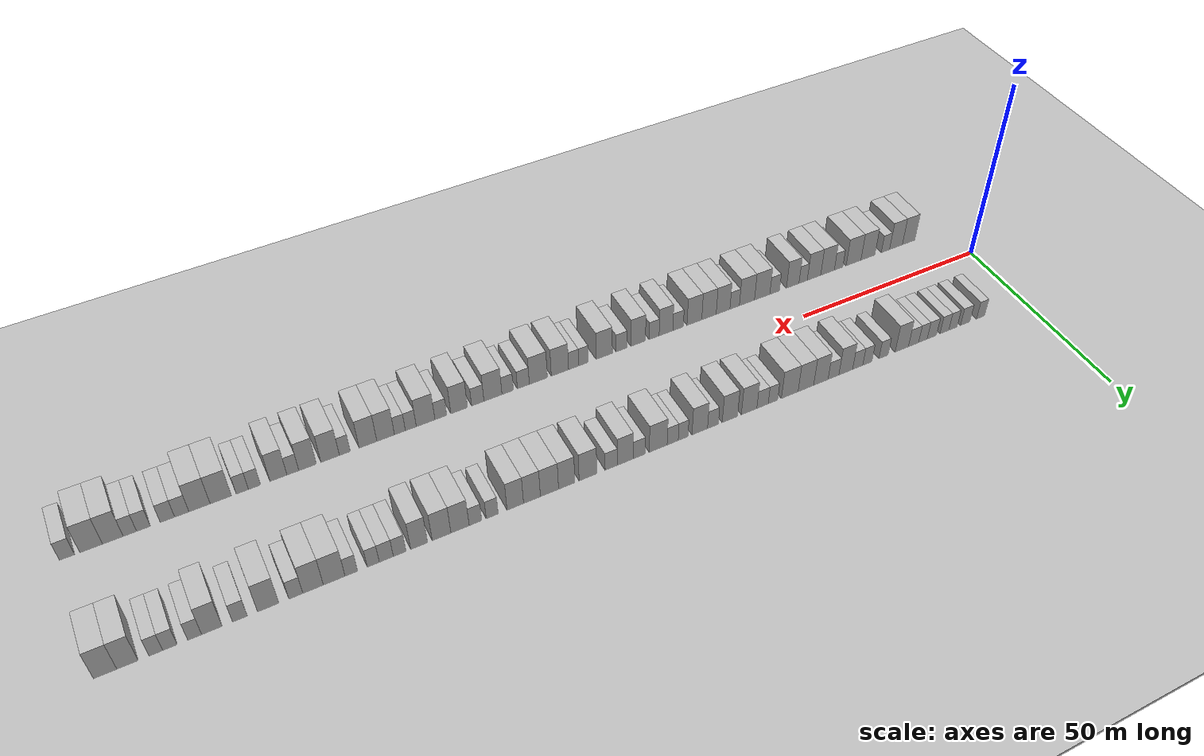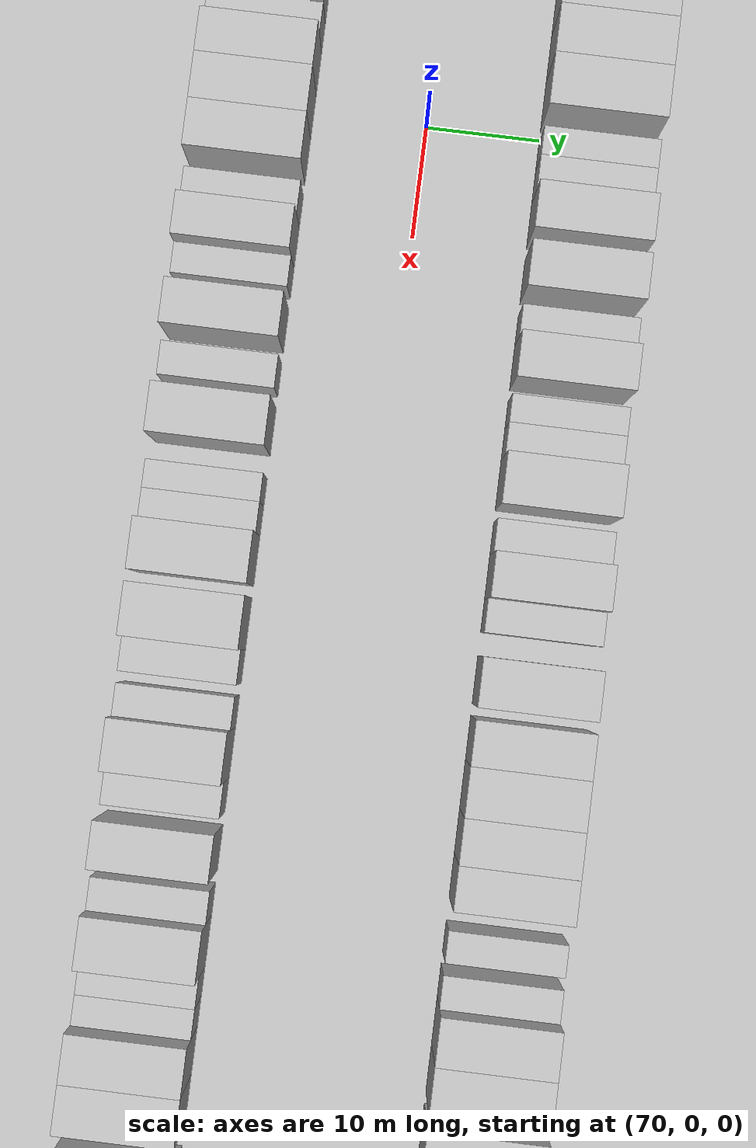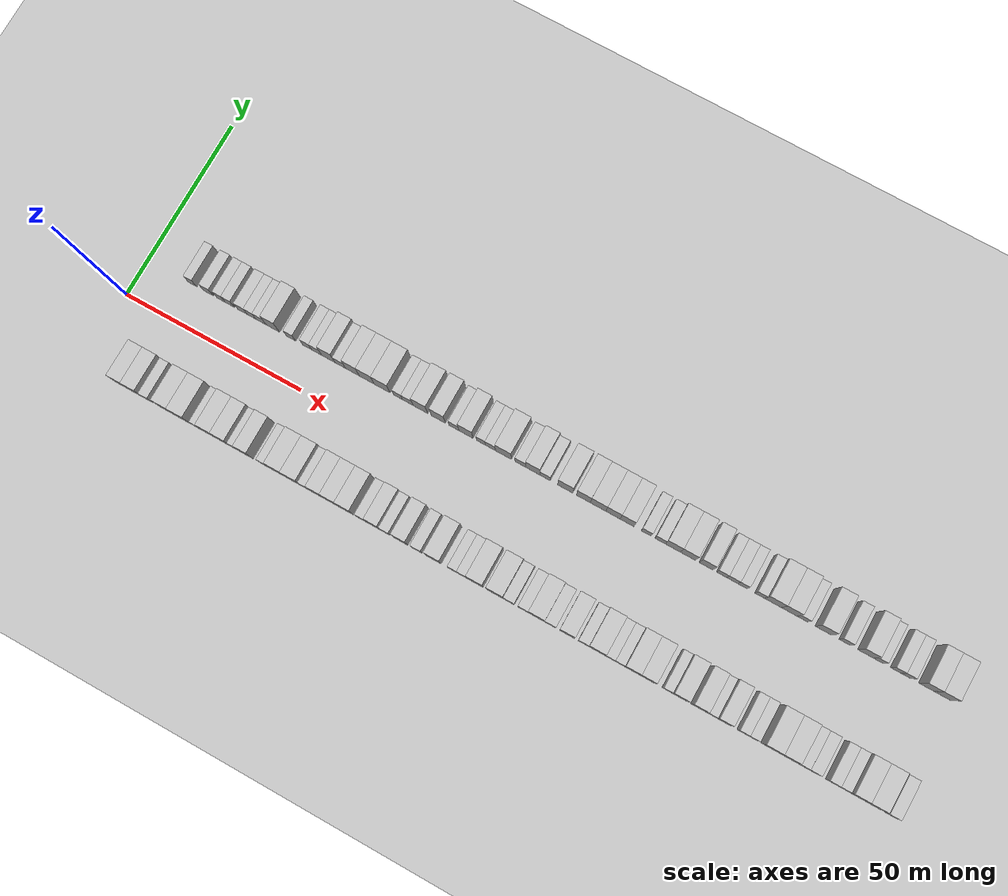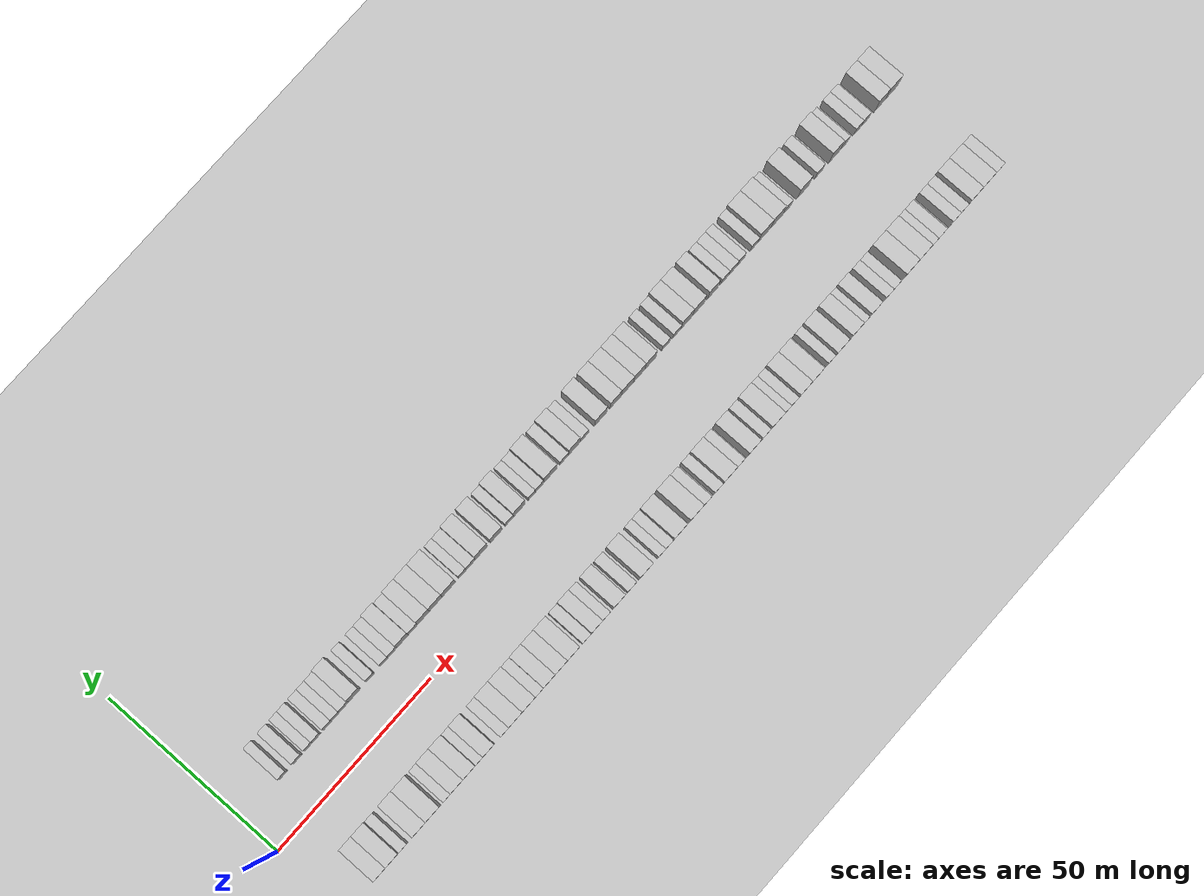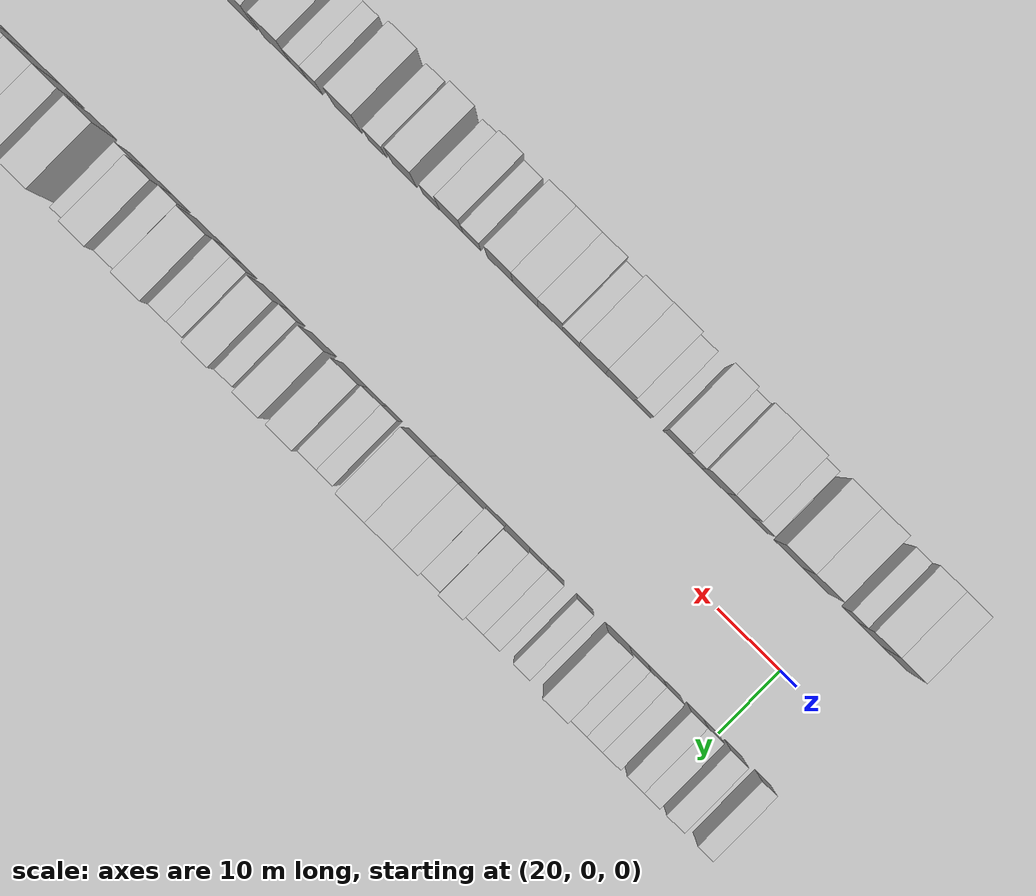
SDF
<?xml version="1.0" encoding="utf-8"?>

<sdf version="1.6">

   <world name="default">

      <gui fullscreen="0">

         <camera name="user_camera">

            <pose>-15 0 4.57585 0 0 0</pose>

            <view_controller>orbit</view_controller>

         </camera>

      </gui>

      <scene>

         <sky>

           <clouds>

             <speed>12</speed>

           </clouds>

         </sky>

         <ambient>0.4 0.4 0.4 1</ambient>

         <background>0.7 0.7 0.7 1</background>

         <shadows>1</shadows>

      </scene>

      <gravity>0 0 -9.8066</gravity>

      <magnetic_field>6e-06 2.3e-05 -4.2e-05</magnetic_field>

      <physics default="0" name="default_physics" type="ode">

         <ode>

            <solver>

               <type>quick</type>

               <iters>10</iters>

               <sor>1.0</sor>

               <use_dynamic_moi_rescaling>0</use_dynamic_moi_rescaling>

            </solver>

            <constraints>

               <cfm>0</cfm>

               <erp>0.2</erp>

               <contact_max_correcting_vel>100</contact_max_correcting_vel>

               <contact_surface_layer>0.001</contact_surface_layer>

            </constraints>

         </ode>

         <max_step_size>0.004</max_step_size>

         <real_time_factor>1</real_time_factor>

         <real_time_update_rate>250</real_time_update_rate>

      </physics>

      <light name="sun" type="directional">

         <cast_shadows>1</cast_shadows>

         <pose>0 0 10 0 0 0</pose>

         <diffuse>0.8 0.8 0.8 1</diffuse>

         <specular>0.2 0.2 0.2 1</specular>

         <attenuation>

            <range>1000</range>

            <constant>0.9</constant>

            <linear>0.01</linear>

            <quadratic>0.001</quadratic>

         </attenuation>

         <direction>-0.5 0.1 -0.9</direction>

      </light>

      <include>

         <name>ground_plane_1</name>

         <uri>model://HANNAS_ground_plane</uri>

         <pose>0 0 0  0 0 0</pose>

      </include>

      <include>

         <name>ground_plane_2</name>

         <uri>model://HANNAS_ground_plane</uri>

         <pose>100 0 0  0 0 0</pose>

      </include>

      <model name="building_1">

         <static>1</static>

         <pose frame="">13.2014 15.0000 0 0.000000 0.000000 1.570796</pose>

         <link name="link">

            <pose frame="">0 0 3.00 0 0 0</pose>

            <collision name="collision">

               <geometry>

                  <box>

                     <size>10.0000 2.4029 6.0000</size>

                  </box>

               </geometry>

               <max_contacts>10</max_contacts>

               <surface>

                  <contact>

                     <ode/>

                  </contact>

                  <bounce/>

                  <friction>

                     <torsional>

                        <ode/>

                     </torsional>

                     <ode/>

                  </friction>

               </surface>

            </collision>

            <visual name="visual">

               <cast_shadows>0</cast_shadows>

               <geometry>

                  <box>

                     <size>10.0000 2.4029 6.0000</size>

                  </box>

               </geometry>

               <material>

                  <script>

                     <uri>model://HANNAS_wall/materials/scripts</uri>

                     <uri>model://HANNAS_wall/materials/textures</uri>

                     <name>vrc/HANNAS_wall</name>

                  </script>

               </material>

            </visual>

            <self_collide>0</self_collide>

            <enable_wind>0</enable_wind>

            <kinematic>0</kinematic>

         </link>

      </model>

      <model name="building_2">

         <static>1</static>

         <pose frame="">17.7954 15.0000 0 0.000000 0.000000 1.570796</pose>

         <link name="link">

            <pose frame="">0 0 3.00 0 0 0</pose>

            <collision name="collision">

               <geometry>

                  <box>

                     <size>10.0000 2.7850 6.0000</size>

                  </box>

               </geometry>

               <max_contacts>10</max_contacts>

               <surface>

                  <contact>

                     <ode/>

                  </contact>

                  <bounce/>

                  <friction>

                     <torsional>

                        <ode/>

                     </torsional>

                     <ode/>

                  </friction>

               </surface>

            </collision>

            <visual name="visual">

               <cast_shadows>0</cast_shadows>

               <geometry>

                  <box>

                     <size>10.0000 2.7850 6.0000</size>

                  </box>

               </geometry>

               <material>

                  <script>

                     <uri>model://HANNAS_wall/materials/scripts</uri>

                     <uri>model://HANNAS_wall/materials/textures</uri>

                     <name>vrc/HANNAS_wall</name>

                  </script>

               </material>

            </visual>

            <self_collide>0</self_collide>

            <enable_wind>0</enable_wind>

            <kinematic>0</kinematic>

         </link>

      </model>

      <model name="building_3">

         <static>1</static>

         <pose frame="">21.4154 15.0000 0 0.000000 0.000000 1.570796</pose>

         <link name="link">

            <pose frame="">0 0 3.00 0 0 0</pose>

            <collision name="collision">

               <geometry>

                  <box>

                     <size>10.0000 2.4551 6.0000</size>

                  </box>

               </geometry>

               <max_contacts>10</max_contacts>

               <surface>

                  <contact>

                     <ode/>

                  </contact>

                  <bounce/>

                  <friction>

                     <torsional>

                        <ode/>

                     </torsional>

                     <ode/>

                  </friction>

               </surface>

            </collision>

            <visual name="visual">

               <cast_shadows>0</cast_shadows>

               <geometry>

                  <box>

                     <size>10.0000 2.4551 6.0000</size>

                  </box>

               </geometry>

               <material>

                  <script>

                     <uri>model://HANNAS_wall/materials/scripts</uri>

                     <uri>model://HANNAS_wall/materials/textures</uri>

                     <name>vrc/HANNAS_wall</name>

                  </script>

               </material>

            </visual>

            <self_collide>0</self_collide>

            <enable_wind>0</enable_wind>

            <kinematic>0</kinematic>

         </link>

      </model>

      <model name="building_4">

         <static>1</static>

         <pose frame="">23.9385 15.0000 0 0.000000 0.000000 1.570796</pose>

         <link name="link">

            <pose frame="">0 0 3.00 0 0 0</pose>

            <collision name="collision">

               <geometry>

                  <box>

                     <size>10.0000 2.5911 6.0000</size>

                  </box>

               </geometry>

               <max_contacts>10</max_contacts>

               <surface>

                  <contact>

                     <ode/>

                  </contact>

                  <bounce/>

                  <friction>

                     <torsional>

                        <ode/>

                     </torsional>

                     <ode/>

                  </friction>

               </surface>

            </collision>

            <visual name="visual">

               <cast_shadows>0</cast_shadows>

               <geometry>

                  <box>

                     <size>10.0000 2.5911 6.0000</size>

                  </box>

               </geometry>

               <material>

                  <script>

                     <uri>model://HANNAS_wall/materials/scripts</uri>

                     <uri>model://HANNAS_wall/materials/textures</uri>

                     <name>vrc/HANNAS_wall</name>

                  </script>

               </material>

            </visual>

            <self_collide>0</self_collide>

            <enable_wind>0</enable_wind>

            <kinematic>0</kinematic>

         </link>

      </model>

      <model name="building_5">

         <static>1</static>

         <pose frame="">27.6037 15.0000 0 0.000000 0.000000 1.570796</pose>

         <link name="link">

            <pose frame="">0 0 3.00 0 0 0</pose>

            <collision name="collision">

               <geometry>

                  <box>

                     <size>10.0000 2.7393 6.0000</size>

                  </box>

               </geometry>

               <max_contacts>10</max_contacts>

               <surface>

                  <contact>

                     <ode/>

                  </contact>

                  <bounce/>

                  <friction>

                     <torsional>

                        <ode/>

                     </torsional>

                     <ode/>

                  </friction>

               </surface>

            </collision>

            <visual name="visual">

               <cast_shadows>0</cast_shadows>

               <geometry>

                  <box>

                     <size>10.0000 2.7393 6.0000</size>

                  </box>

               </geometry>

               <material>

                  <script>

                     <uri>model://HANNAS_wall/materials/scripts</uri>

                     <uri>model://HANNAS_wall/materials/textures</uri>

                     <name>vrc/HANNAS_wall</name>

                  </script>

               </material>

            </visual>

            <self_collide>0</self_collide>

            <enable_wind>0</enable_wind>

            <kinematic>0</kinematic>

         </link>

      </model>

      <model name="building_6">

         <static>1</static>

         <pose frame="">30.2066 15.0000 0 0.000000 0.000000 1.570796</pose>

         <link name="link">

            <pose frame="">0 0 3.00 0 0 0</pose>

            <collision name="collision">

               <geometry>

                  <box>

                     <size>10.0000 2.4665 6.0000</size>

                  </box>

               </geometry>

               <max_contacts>10</max_contacts>

               <surface>

                  <contact>

                     <ode/>

                  </contact>

                  <bounce/>

                  <friction>

                     <torsional>

                        <ode/>

                     </torsional>

                     <ode/>

                  </friction>

               </surface>

            </collision>

            <visual name="visual">

               <cast_shadows>0</cast_shadows>

               <geometry>

                  <box>

                     <size>10.0000 2.4665 6.0000</size>

                  </box>

               </geometry>

               <material>

                  <script>

                     <uri>model://HANNAS_wall/materials/scripts</uri>

                     <uri>model://HANNAS_wall/materials/textures</uri>

                     <name>vrc/HANNAS_wall</name>

                  </script>

               </material>

            </visual>

            <self_collide>0</self_collide>

            <enable_wind>0</enable_wind>

            <kinematic>0</kinematic>

         </link>

      </model>

      <model name="building_7">

         <static>1</static>

         <pose frame="">32.9014 15.0000 0 0.000000 0.000000 1.570796</pose>

         <link name="link">

            <pose frame="">0 0 3.00 0 0 0</pose>

            <collision name="collision">

               <geometry>

                  <box>

                     <size>10.0000 2.9229 6.0000</size>

                  </box>

               </geometry>

               <max_contacts>10</max_contacts>

               <surface>

                  <contact>

                     <ode/>

                  </contact>

                  <bounce/>

                  <friction>

                     <torsional>

                        <ode/>

                     </torsional>

                     <ode/>

                  </friction>

               </surface>

            </collision>

            <visual name="visual">

               <cast_shadows>0</cast_shadows>

               <geometry>

                  <box>

                     <size>10.0000 2.9229 6.0000</size>

                  </box>

               </geometry>

               <material>

                  <script>

                     <uri>model://HANNAS_wall/materials/scripts</uri>

                     <uri>model://HANNAS_wall/materials/textures</uri>

                     <name>vrc/HANNAS_wall</name>

                  </script>

               </material>

            </visual>

            <self_collide>0</self_collide>

            <enable_wind>0</enable_wind>

            <kinematic>0</kinematic>

         </link>

      </model>

      <model name="building_8">

         <static>1</static>

         <pose frame="">36.2609 15.0000 0 0.000000 0.000000 1.570796</pose>

         <link name="link">

            <pose frame="">0 0 4.50 0 0 0</pose>

            <collision name="collision">

               <geometry>

                  <box>

                     <size>10.0000 3.7962 9.0000</size>

                  </box>

               </geometry>

               <max_contacts>10</max_contacts>

               <surface>

                  <contact>

                     <ode/>

                  </contact>

                  <bounce/>

                  <friction>

                     <torsional>

                        <ode/>

                     </torsional>

                     <ode/>

                  </friction>

               </surface>

            </collision>

            <visual name="visual">

               <cast_shadows>0</cast_shadows>

               <geometry>

                  <box>

                     <size>10.0000 3.7962 9.0000</size>

                  </box>

               </geometry>

               <material>

                  <script>

                     <uri>model://HANNAS_wall/materials/scripts</uri>

                     <uri>model://HANNAS_wall/materials/textures</uri>

                     <name>vrc/HANNAS_wall</name>

                  </script>

               </material>

            </visual>

            <self_collide>0</self_collide>

            <enable_wind>0</enable_wind>

            <kinematic>0</kinematic>

         </link>

      </model>

      <model name="building_9">

         <static>1</static>

         <pose frame="">41.4479 15.0000 0 0.000000 0.000000 1.570796</pose>

         <link name="link">

            <pose frame="">0 0 3.00 0 0 0</pose>

            <collision name="collision">

               <geometry>

                  <box>

                     <size>10.0000 2.5777 6.0000</size>

                  </box>

               </geometry>

               <max_contacts>10</max_contacts>

               <surface>

                  <contact>

                     <ode/>

                  </contact>

                  <bounce/>

                  <friction>

                     <torsional>

                        <ode/>

                     </torsional>

                     <ode/>

                  </friction>

               </surface>

            </collision>

            <visual name="visual">

               <cast_shadows>0</cast_shadows>

               <geometry>

                  <box>

                     <size>10.0000 2.5777 6.0000</size>

                  </box>

               </geometry>

               <material>

                  <script>

                     <uri>model://HANNAS_wall/materials/scripts</uri>

                     <uri>model://HANNAS_wall/materials/textures</uri>

                     <name>vrc/HANNAS_wall</name>

                  </script>

               </material>

            </visual>

            <self_collide>0</self_collide>

            <enable_wind>0</enable_wind>

            <kinematic>0</kinematic>

         </link>

      </model>

      <model name="building_10">

         <static>1</static>

         <pose frame="">45.9956 15.0000 0 0.000000 0.000000 1.570796</pose>

         <link name="link">

            <pose frame="">0 0 3.00 0 0 0</pose>

            <collision name="collision">

               <geometry>

                  <box>

                     <size>10.0000 2.5177 6.0000</size>

                  </box>

               </geometry>

               <max_contacts>10</max_contacts>

               <surface>

                  <contact>

                     <ode/>

                  </contact>

                  <bounce/>

                  <friction>

                     <torsional>

                        <ode/>

                     </torsional>

                     <ode/>

                  </friction>

               </surface>

            </collision>

            <visual name="visual">

               <cast_shadows>0</cast_shadows>

               <geometry>

                  <box>

                     <size>10.0000 2.5177 6.0000</size>

                  </box>

               </geometry>

               <material>

                  <script>

                     <uri>model://HANNAS_wall/materials/scripts</uri>

                     <uri>model://HANNAS_wall/materials/textures</uri>

                     <name>vrc/HANNAS_wall</name>

                  </script>

               </material>

            </visual>

            <self_collide>0</self_collide>

            <enable_wind>0</enable_wind>

            <kinematic>0</kinematic>

         </link>

      </model>

      <model name="building_11">

         <static>1</static>

         <pose frame="">48.6783 15.0000 0 0.000000 0.000000 1.570796</pose>

         <link name="link">

            <pose frame="">0 0 3.00 0 0 0</pose>

            <collision name="collision">

               <geometry>

                  <box>

                     <size>10.0000 2.8477 6.0000</size>

                  </box>

               </geometry>

               <max_contacts>10</max_contacts>

               <surface>

                  <contact>

                     <ode/>

                  </contact>

                  <bounce/>

                  <friction>

                     <torsional>

                        <ode/>

                     </torsional>

                     <ode/>

                  </friction>

               </surface>

            </collision>

            <visual name="visual">

               <cast_shadows>0</cast_shadows>

               <geometry>

                  <box>

                     <size>10.0000 2.8477 6.0000</size>

                  </box>

               </geometry>

               <material>

                  <script>

                     <uri>model://HANNAS_wall/materials/scripts</uri>

                     <uri>model://HANNAS_wall/materials/textures</uri>

                     <name>vrc/HANNAS_wall</name>

                  </script>

               </material>

            </visual>

            <self_collide>0</self_collide>

            <enable_wind>0</enable_wind>

            <kinematic>0</kinematic>

         </link>

      </model>

      <model name="building_12">

         <static>1</static>

         <pose frame="">51.9933 15.0000 0 0.000000 0.000000 1.570796</pose>

         <link name="link">

            <pose frame="">0 0 4.50 0 0 0</pose>

            <collision name="collision">

               <geometry>

                  <box>

                     <size>10.0000 3.7822 9.0000</size>

                  </box>

               </geometry>

               <max_contacts>10</max_contacts>

               <surface>

                  <contact>

                     <ode/>

                  </contact>

                  <bounce/>

                  <friction>

                     <torsional>

                        <ode/>

                     </torsional>

                     <ode/>

                  </friction>

               </surface>

            </collision>

            <visual name="visual">

               <cast_shadows>0</cast_shadows>

               <geometry>

                  <box>

                     <size>10.0000 3.7822 9.0000</size>

                  </box>

               </geometry>

               <material>

                  <script>

                     <uri>model://HANNAS_wall/materials/scripts</uri>

                     <uri>model://HANNAS_wall/materials/textures</uri>

                     <name>vrc/HANNAS_wall</name>

                  </script>

               </material>

            </visual>

            <self_collide>0</self_collide>

            <enable_wind>0</enable_wind>

            <kinematic>0</kinematic>

         </link>

      </model>

      <model name="building_13">

         <static>1</static>

         <pose frame="">55.3688 15.0000 0 0.000000 0.000000 1.570796</pose>

         <link name="link">

            <pose frame="">0 0 3.00 0 0 0</pose>

            <collision name="collision">

               <geometry>

                  <box>

                     <size>10.0000 2.9688 6.0000</size>

                  </box>

               </geometry>

               <max_contacts>10</max_contacts>

               <surface>

                  <contact>

                     <ode/>

                  </contact>

                  <bounce/>

                  <friction>

                     <torsional>

                        <ode/>

                     </torsional>

                     <ode/>

                  </friction>

               </surface>

            </collision>

            <visual name="visual">

               <cast_shadows>0</cast_shadows>

               <geometry>

                  <box>

                     <size>10.0000 2.9688 6.0000</size>

                  </box>

               </geometry>

               <material>

                  <script>

                     <uri>model://HANNAS_wall/materials/scripts</uri>

                     <uri>model://HANNAS_wall/materials/textures</uri>

                     <name>vrc/HANNAS_wall</name>

                  </script>

               </material>

            </visual>

            <self_collide>0</self_collide>

            <enable_wind>0</enable_wind>

            <kinematic>0</kinematic>

         </link>

      </model>

      <model name="building_14">

         <static>1</static>

         <pose frame="">58.8022 15.0000 0 0.000000 0.000000 1.570796</pose>

         <link name="link">

            <pose frame="">0 0 4.50 0 0 0</pose>

            <collision name="collision">

               <geometry>

                  <box>

                     <size>10.0000 3.8981 9.0000</size>

                  </box>

               </geometry>

               <max_contacts>10</max_contacts>

               <surface>

                  <contact>

                     <ode/>

                  </contact>

                  <bounce/>

                  <friction>

                     <torsional>

                        <ode/>

                     </torsional>

                     <ode/>

                  </friction>

               </surface>

            </collision>

            <visual name="visual">

               <cast_shadows>0</cast_shadows>

               <geometry>

                  <box>

                     <size>10.0000 3.8981 9.0000</size>

                  </box>

               </geometry>

               <material>

                  <script>

                     <uri>model://HANNAS_wall/materials/scripts</uri>

                     <uri>model://HANNAS_wall/materials/textures</uri>

                     <name>vrc/HANNAS_wall</name>

                  </script>

               </material>

            </visual>

            <self_collide>0</self_collide>

            <enable_wind>0</enable_wind>

            <kinematic>0</kinematic>

         </link>

      </model>

      <model name="building_15">

         <static>1</static>

         <pose frame="">62.8452 15.0000 0 0.000000 0.000000 1.570796</pose>

         <link name="link">

            <pose frame="">0 0 4.50 0 0 0</pose>

            <collision name="collision">

               <geometry>

                  <box>

                     <size>10.0000 4.1878 9.0000</size>

                  </box>

               </geometry>

               <max_contacts>10</max_contacts>

               <surface>

                  <contact>

                     <ode/>

                  </contact>

                  <bounce/>

                  <friction>

                     <torsional>

                        <ode/>

                     </torsional>

                     <ode/>

                  </friction>

               </surface>

            </collision>

            <visual name="visual">

               <cast_shadows>0</cast_shadows>

               <geometry>

                  <box>

                     <size>10.0000 4.1878 9.0000</size>

                  </box>

               </geometry>

               <material>

                  <script>

                     <uri>model://HANNAS_wall/materials/scripts</uri>

                     <uri>model://HANNAS_wall/materials/textures</uri>

                     <name>vrc/HANNAS_wall</name>

                  </script>

               </material>

            </visual>

            <self_collide>0</self_collide>

            <enable_wind>0</enable_wind>

            <kinematic>0</kinematic>

         </link>

      </model>

      <model name="building_16">

         <static>1</static>

         <pose frame="">67.1615 15.0000 0 0.000000 0.000000 1.570796</pose>

         <link name="link">

            <pose frame="">0 0 4.50 0 0 0</pose>

            <collision name="collision">

               <geometry>

                  <box>

                     <size>10.0000 4.4448 9.0000</size>

                  </box>

               </geometry>

               <max_contacts>10</max_contacts>

               <surface>

                  <contact>

                     <ode/>

                  </contact>

                  <bounce/>

                  <friction>

                     <torsional>

                        <ode/>

                     </torsional>

                     <ode/>

                  </friction>

               </surface>

            </collision>

            <visual name="visual">

               <cast_shadows>0</cast_shadows>

               <geometry>

                  <box>

                     <size>10.0000 4.4448 9.0000</size>

                  </box>

               </geometry>

               <material>

                  <script>

                     <uri>model://HANNAS_wall/materials/scripts</uri>

                     <uri>model://HANNAS_wall/materials/textures</uri>

                     <name>vrc/HANNAS_wall</name>

                  </script>

               </material>

            </visual>

            <self_collide>0</self_collide>

            <enable_wind>0</enable_wind>

            <kinematic>0</kinematic>

         </link>

      </model>

      <model name="building_17">

         <static>1</static>

         <pose frame="">71.6301 15.0000 0 0.000000 0.000000 1.570796</pose>

         <link name="link">

            <pose frame="">0 0 3.00 0 0 0</pose>

            <collision name="collision">

               <geometry>

                  <box>

                     <size>10.0000 2.4925 6.0000</size>

                  </box>

               </geometry>

               <max_contacts>10</max_contacts>

               <surface>

                  <contact>

                     <ode/>

                  </contact>

                  <bounce/>

                  <friction>

                     <torsional>

                        <ode/>

                     </torsional>

                     <ode/>

                  </friction>

               </surface>

            </collision>

            <visual name="visual">

               <cast_shadows>0</cast_shadows>

               <geometry>

                  <box>

                     <size>10.0000 2.4925 6.0000</size>

                  </box>

               </geometry>

               <material>

                  <script>

                     <uri>model://HANNAS_wall/materials/scripts</uri>

                     <uri>model://HANNAS_wall/materials/textures</uri>

                     <name>vrc/HANNAS_wall</name>

                  </script>

               </material>

            </visual>

            <self_collide>0</self_collide>

            <enable_wind>0</enable_wind>

            <kinematic>0</kinematic>

         </link>

      </model>

      <model name="building_18">

         <static>1</static>

         <pose frame="">74.3623 15.0000 0 0.000000 0.000000 1.570796</pose>

         <link name="link">

            <pose frame="">0 0 3.00 0 0 0</pose>

            <collision name="collision">

               <geometry>

                  <box>

                     <size>10.0000 2.9719 6.0000</size>

                  </box>

               </geometry>

               <max_contacts>10</max_contacts>

               <surface>

                  <contact>

                     <ode/>

                  </contact>

                  <bounce/>

                  <friction>

                     <torsional>

                        <ode/>

                     </torsional>

                     <ode/>

                  </friction>

               </surface>

            </collision>

            <visual name="visual">

               <cast_shadows>0</cast_shadows>

               <geometry>

                  <box>

                     <size>10.0000 2.9719 6.0000</size>

                  </box>

               </geometry>

               <material>

                  <script>

                     <uri>model://HANNAS_wall/materials/scripts</uri>

                     <uri>model://HANNAS_wall/materials/textures</uri>

                     <name>vrc/HANNAS_wall</name>

                  </script>

               </material>

            </visual>

            <self_collide>0</self_collide>

            <enable_wind>0</enable_wind>

            <kinematic>0</kinematic>

         </link>

      </model>

      <model name="building_19">

         <static>1</static>

         <pose frame="">77.8619 15.0000 0 0.000000 0.000000 1.570796</pose>

         <link name="link">

            <pose frame="">0 0 4.50 0 0 0</pose>

            <collision name="collision">

               <geometry>

                  <box>

                     <size>10.0000 4.0272 9.0000</size>

                  </box>

               </geometry>

               <max_contacts>10</max_contacts>

               <surface>

                  <contact>

                     <ode/>

                  </contact>

                  <bounce/>

                  <friction>

                     <torsional>

                        <ode/>

                     </torsional>

                     <ode/>

                  </friction>

               </surface>

            </collision>

            <visual name="visual">

               <cast_shadows>0</cast_shadows>

               <geometry>

                  <box>

                     <size>10.0000 4.0272 9.0000</size>

                  </box>

               </geometry>

               <material>

                  <script>

                     <uri>model://HANNAS_wall/materials/scripts</uri>

                     <uri>model://HANNAS_wall/materials/textures</uri>

                     <name>vrc/HANNAS_wall</name>

                  </script>

               </material>

            </visual>

            <self_collide>0</self_collide>

            <enable_wind>0</enable_wind>

            <kinematic>0</kinematic>

         </link>

      </model>

      <model name="building_20">

         <static>1</static>

         <pose frame="">82.8364 15.0000 0 0.000000 0.000000 1.570796</pose>

         <link name="link">

            <pose frame="">0 0 4.50 0 0 0</pose>

            <collision name="collision">

               <geometry>

                  <box>

                     <size>10.0000 3.9218 9.0000</size>

                  </box>

               </geometry>

               <max_contacts>10</max_contacts>

               <surface>

                  <contact>

                     <ode/>

                  </contact>

                  <bounce/>

                  <friction>

                     <torsional>

                        <ode/>

                     </torsional>

                     <ode/>

                  </friction>

               </surface>

            </collision>

            <visual name="visual">

               <cast_shadows>0</cast_shadows>

               <geometry>

                  <box>

                     <size>10.0000 3.9218 9.0000</size>

                  </box>

               </geometry>

               <material>

                  <script>

                     <uri>model://HANNAS_wall/materials/scripts</uri>

                     <uri>model://HANNAS_wall/materials/textures</uri>

                     <name>vrc/HANNAS_wall</name>

                  </script>

               </material>

            </visual>

            <self_collide>0</self_collide>

            <enable_wind>0</enable_wind>

            <kinematic>0</kinematic>

         </link>

      </model>

      <model name="building_21">

         <static>1</static>

         <pose frame="">87.1644 15.0000 0 0.000000 0.000000 1.570796</pose>

         <link name="link">

            <pose frame="">0 0 3.00 0 0 0</pose>

            <collision name="collision">

               <geometry>

                  <box>

                     <size>10.0000 2.7342 6.0000</size>

                  </box>

               </geometry>

               <max_contacts>10</max_contacts>

               <surface>

                  <contact>

                     <ode/>

                  </contact>

                  <bounce/>

                  <friction>

                     <torsional>

                        <ode/>

                     </torsional>

                     <ode/>

                  </friction>

               </surface>

            </collision>

            <visual name="visual">

               <cast_shadows>0</cast_shadows>

               <geometry>

                  <box>

                     <size>10.0000 2.7342 6.0000</size>

                  </box>

               </geometry>

               <material>

                  <script>

                     <uri>model://HANNAS_wall/materials/scripts</uri>

                     <uri>model://HANNAS_wall/materials/textures</uri>

                     <name>vrc/HANNAS_wall</name>

                  </script>

               </material>

            </visual>

            <self_collide>0</self_collide>

            <enable_wind>0</enable_wind>

            <kinematic>0</kinematic>

         </link>

      </model>

      <model name="building_22">

         <static>1</static>

         <pose frame="">90.4941 15.0000 0 0.000000 0.000000 1.570796</pose>

         <link name="link">

            <pose frame="">0 0 4.50 0 0 0</pose>

            <collision name="collision">

               <geometry>

                  <box>

                     <size>10.0000 3.9252 9.0000</size>

                  </box>

               </geometry>

               <max_contacts>10</max_contacts>

               <surface>

                  <contact>

                     <ode/>

                  </contact>

                  <bounce/>

                  <friction>

                     <torsional>

                        <ode/>

                     </torsional>

                     <ode/>

                  </friction>

               </surface>

            </collision>

            <visual name="visual">

               <cast_shadows>0</cast_shadows>

               <geometry>

                  <box>

                     <size>10.0000 3.9252 9.0000</size>

                  </box>

               </geometry>

               <material>

                  <script>

                     <uri>model://HANNAS_wall/materials/scripts</uri>

                     <uri>model://HANNAS_wall/materials/textures</uri>

                     <name>vrc/HANNAS_wall</name>

                  </script>

               </material>

            </visual>

            <self_collide>0</self_collide>

            <enable_wind>0</enable_wind>

            <kinematic>0</kinematic>

         </link>

      </model>

      <model name="building_23">

         <static>1</static>

         <pose frame="">94.6765 15.0000 0 0.000000 0.000000 1.570796</pose>

         <link name="link">

            <pose frame="">0 0 3.00 0 0 0</pose>

            <collision name="collision">

               <geometry>

                  <box>

                     <size>10.0000 2.4396 6.0000</size>

                  </box>

               </geometry>

               <max_contacts>10</max_contacts>

               <surface>

                  <contact>

                     <ode/>

                  </contact>

                  <bounce/>

                  <friction>

                     <torsional>

                        <ode/>

                     </torsional>

                     <ode/>

                  </friction>

               </surface>

            </collision>

            <visual name="visual">

               <cast_shadows>0</cast_shadows>

               <geometry>

                  <box>

                     <size>10.0000 2.4396 6.0000</size>

                  </box>

               </geometry>

               <material>

                  <script>

                     <uri>model://HANNAS_wall/materials/scripts</uri>

                     <uri>model://HANNAS_wall/materials/textures</uri>

                     <name>vrc/HANNAS_wall</name>

                  </script>

               </material>

            </visual>

            <self_collide>0</self_collide>

            <enable_wind>0</enable_wind>

            <kinematic>0</kinematic>

         </link>

      </model>

      <model name="building_24">

         <static>1</static>

         <pose frame="">97.2753 15.0000 0 0.000000 0.000000 1.570796</pose>

         <link name="link">

            <pose frame="">0 0 3.00 0 0 0</pose>

            <collision name="collision">

               <geometry>

                  <box>

                     <size>10.0000 2.7580 6.0000</size>

                  </box>

               </geometry>

               <max_contacts>10</max_contacts>

               <surface>

                  <contact>

                     <ode/>

                  </contact>

                  <bounce/>

                  <friction>

                     <torsional>

                        <ode/>

                     </torsional>

                     <ode/>

                  </friction>

               </surface>

            </collision>

            <visual name="visual">

               <cast_shadows>0</cast_shadows>

               <geometry>

                  <box>

                     <size>10.0000 2.7580 6.0000</size>

                  </box>

               </geometry>

               <material>

                  <script>

                     <uri>model://HANNAS_wall/materials/scripts</uri>

                     <uri>model://HANNAS_wall/materials/textures</uri>

                     <name>vrc/HANNAS_wall</name>

                  </script>

               </material>

            </visual>

            <self_collide>0</self_collide>

            <enable_wind>0</enable_wind>

            <kinematic>0</kinematic>

         </link>

      </model>

      <model name="building_25">

         <static>1</static>

         <pose frame="">100.8544 15.0000 0 0.000000 0.000000 1.570796</pose>

         <link name="link">

            <pose frame="">0 0 4.50 0 0 0</pose>

            <collision name="collision">

               <geometry>

                  <box>

                     <size>10.0000 4.4003 9.0000</size>

                  </box>

               </geometry>

               <max_contacts>10</max_contacts>

               <surface>

                  <contact>

                     <ode/>

                  </contact>

                  <bounce/>

                  <friction>

                     <torsional>

                        <ode/>

                     </torsional>

                     <ode/>

                  </friction>

               </surface>

            </collision>

            <visual name="visual">

               <cast_shadows>0</cast_shadows>

               <geometry>

                  <box>

                     <size>10.0000 4.4003 9.0000</size>

                  </box>

               </geometry>

               <material>

                  <script>

                     <uri>model://HANNAS_wall/materials/scripts</uri>

                     <uri>model://HANNAS_wall/materials/textures</uri>

                     <name>vrc/HANNAS_wall</name>

                  </script>

               </material>

            </visual>

            <self_collide>0</self_collide>

            <enable_wind>0</enable_wind>

            <kinematic>0</kinematic>

         </link>

      </model>

      <model name="building_26">

         <static>1</static>

         <pose frame="">105.5059 15.0000 0 0.000000 0.000000 1.570796</pose>

         <link name="link">

            <pose frame="">0 0 3.00 0 0 0</pose>

            <collision name="collision">

               <geometry>

                  <box>

                     <size>10.0000 2.9027 6.0000</size>

                  </box>

               </geometry>

               <max_contacts>10</max_contacts>

               <surface>

                  <contact>

                     <ode/>

                  </contact>

                  <bounce/>

                  <friction>

                     <torsional>

                        <ode/>

                     </torsional>

                     <ode/>

                  </friction>

               </surface>

            </collision>

            <visual name="visual">

               <cast_shadows>0</cast_shadows>

               <geometry>

                  <box>

                     <size>10.0000 2.9027 6.0000</size>

                  </box>

               </geometry>

               <material>

                  <script>

                     <uri>model://HANNAS_wall/materials/scripts</uri>

                     <uri>model://HANNAS_wall/materials/textures</uri>

                     <name>vrc/HANNAS_wall</name>

                  </script>

               </material>

            </visual>

            <self_collide>0</self_collide>

            <enable_wind>0</enable_wind>

            <kinematic>0</kinematic>

         </link>

      </model>

      <model name="building_27">

         <static>1</static>

         <pose frame="">108.8884 15.0000 0 0.000000 0.000000 1.570796</pose>

         <link name="link">

            <pose frame="">0 0 4.50 0 0 0</pose>

            <collision name="collision">

               <geometry>

                  <box>

                     <size>10.0000 3.8622 9.0000</size>

                  </box>

               </geometry>

               <max_contacts>10</max_contacts>

               <surface>

                  <contact>

                     <ode/>

                  </contact>

                  <bounce/>

                  <friction>

                     <torsional>

                        <ode/>

                     </torsional>

                     <ode/>

                  </friction>

               </surface>

            </collision>

            <visual name="visual">

               <cast_shadows>0</cast_shadows>

               <geometry>

                  <box>

                     <size>10.0000 3.8622 9.0000</size>

                  </box>

               </geometry>

               <material>

                  <script>

                     <uri>model://HANNAS_wall/materials/scripts</uri>

                     <uri>model://HANNAS_wall/materials/textures</uri>

                     <name>vrc/HANNAS_wall</name>

                  </script>

               </material>

            </visual>

            <self_collide>0</self_collide>

            <enable_wind>0</enable_wind>

            <kinematic>0</kinematic>

         </link>

      </model>

      <model name="building_28">

         <static>1</static>

         <pose frame="">112.2653 15.0000 0 0.000000 0.000000 1.570796</pose>

         <link name="link">

            <pose frame="">0 0 3.00 0 0 0</pose>

            <collision name="collision">

               <geometry>

                  <box>

                     <size>10.0000 2.8916 6.0000</size>

                  </box>

               </geometry>

               <max_contacts>10</max_contacts>

               <surface>

                  <contact>

                     <ode/>

                  </contact>

                  <bounce/>

                  <friction>

                     <torsional>

                        <ode/>

                     </torsional>

                     <ode/>

                  </friction>

               </surface>

            </collision>

            <visual name="visual">

               <cast_shadows>0</cast_shadows>

               <geometry>

                  <box>

                     <size>10.0000 2.8916 6.0000</size>

                  </box>

               </geometry>

               <material>

                  <script>

                     <uri>model://HANNAS_wall/materials/scripts</uri>

                     <uri>model://HANNAS_wall/materials/textures</uri>

                     <name>vrc/HANNAS_wall</name>

                  </script>

               </material>

            </visual>

            <self_collide>0</self_collide>

            <enable_wind>0</enable_wind>

            <kinematic>0</kinematic>

         </link>

      </model>

      <model name="building_29">

         <static>1</static>

         <pose frame="">117.7975 15.0000 0 0.000000 0.000000 1.570796</pose>

         <link name="link">

            <pose frame="">0 0 4.50 0 0 0</pose>

            <collision name="collision">

               <geometry>

                  <box>

                     <size>10.0000 4.1728 9.0000</size>

                  </box>

               </geometry>

               <max_contacts>10</max_contacts>

               <surface>

                  <contact>

                     <ode/>

                  </contact>

                  <bounce/>

                  <friction>

                     <torsional>

                        <ode/>

                     </torsional>

                     <ode/>

                  </friction>

               </surface>

            </collision>

            <visual name="visual">

               <cast_shadows>0</cast_shadows>

               <geometry>

                  <box>

                     <size>10.0000 4.1728 9.0000</size>

                  </box>

               </geometry>

               <material>

                  <script>

                     <uri>model://HANNAS_wall/materials/scripts</uri>

                     <uri>model://HANNAS_wall/materials/textures</uri>

                     <name>vrc/HANNAS_wall</name>

                  </script>

               </material>

            </visual>

            <self_collide>0</self_collide>

            <enable_wind>0</enable_wind>

            <kinematic>0</kinematic>

         </link>

      </model>

      <model name="building_30">

         <static>1</static>

         <pose frame="">122.7850 15.0000 0 0.000000 0.000000 1.570796</pose>

         <link name="link">

            <pose frame="">0 0 4.50 0 0 0</pose>

            <collision name="collision">

               <geometry>

                  <box>

                     <size>10.0000 3.8023 9.0000</size>

                  </box>

               </geometry>

               <max_contacts>10</max_contacts>

               <surface>

                  <contact>

                     <ode/>

                  </contact>

                  <bounce/>

                  <friction>

                     <torsional>

                        <ode/>

                     </torsional>

                     <ode/>

                  </friction>

               </surface>

            </collision>

            <visual name="visual">

               <cast_shadows>0</cast_shadows>

               <geometry>

                  <box>

                     <size>10.0000 3.8023 9.0000</size>

                  </box>

               </geometry>

               <material>

                  <script>

                     <uri>model://HANNAS_wall/materials/scripts</uri>

                     <uri>model://HANNAS_wall/materials/textures</uri>

                     <name>vrc/HANNAS_wall</name>

                  </script>

               </material>

            </visual>

            <self_collide>0</self_collide>

            <enable_wind>0</enable_wind>

            <kinematic>0</kinematic>

         </link>

      </model>

      <model name="building_31">

         <static>1</static>

         <pose frame="">126.7876 15.0000 0 0.000000 0.000000 1.570796</pose>

         <link name="link">

            <pose frame="">0 0 4.50 0 0 0</pose>

            <collision name="collision">

               <geometry>

                  <box>

                     <size>10.0000 4.2027 9.0000</size>

                  </box>

               </geometry>

               <max_contacts>10</max_contacts>

               <surface>

                  <contact>

                     <ode/>

                  </contact>

                  <bounce/>

                  <friction>

                     <torsional>

                        <ode/>

                     </torsional>

                     <ode/>

                  </friction>

               </surface>

            </collision>

            <visual name="visual">

               <cast_shadows>0</cast_shadows>

               <geometry>

                  <box>

                     <size>10.0000 4.2027 9.0000</size>

                  </box>

               </geometry>

               <material>

                  <script>

                     <uri>model://HANNAS_wall/materials/scripts</uri>

                     <uri>model://HANNAS_wall/materials/textures</uri>

                     <name>vrc/HANNAS_wall</name>

                  </script>

               </material>

            </visual>

            <self_collide>0</self_collide>

            <enable_wind>0</enable_wind>

            <kinematic>0</kinematic>

         </link>

      </model>

      <model name="building_32">

         <static>1</static>

         <pose frame="">130.8163 15.0000 0 0.000000 0.000000 1.570796</pose>

         <link name="link">

            <pose frame="">0 0 4.50 0 0 0</pose>

            <collision name="collision">

               <geometry>

                  <box>

                     <size>10.0000 3.8548 9.0000</size>

                  </box>

               </geometry>

               <max_contacts>10</max_contacts>

               <surface>

                  <contact>

                     <ode/>

                  </contact>

                  <bounce/>

                  <friction>

                     <torsional>

                        <ode/>

                     </torsional>

                     <ode/>

                  </friction>

               </surface>

            </collision>

            <visual name="visual">

               <cast_shadows>0</cast_shadows>

               <geometry>

                  <box>

                     <size>10.0000 3.8548 9.0000</size>

                  </box>

               </geometry>

               <material>

                  <script>

                     <uri>model://HANNAS_wall/materials/scripts</uri>

                     <uri>model://HANNAS_wall/materials/textures</uri>

                     <name>vrc/HANNAS_wall</name>

                  </script>

               </material>

            </visual>

            <self_collide>0</self_collide>

            <enable_wind>0</enable_wind>

            <kinematic>0</kinematic>

         </link>

      </model>

      <model name="building_33">

         <static>1</static>

         <pose frame="">134.6118 15.0000 0 0.000000 0.000000 1.570796</pose>

         <link name="link">

            <pose frame="">0 0 4.50 0 0 0</pose>

            <collision name="collision">

               <geometry>

                  <box>

                     <size>10.0000 3.7360 9.0000</size>

                  </box>

               </geometry>

               <max_contacts>10</max_contacts>

               <surface>

                  <contact>

                     <ode/>

                  </contact>

                  <bounce/>

                  <friction>

                     <torsional>

                        <ode/>

                     </torsional>

                     <ode/>

                  </friction>

               </surface>

            </collision>

            <visual name="visual">

               <cast_shadows>0</cast_shadows>

               <geometry>

                  <box>

                     <size>10.0000 3.7360 9.0000</size>

                  </box>

               </geometry>

               <material>

                  <script>

                     <uri>model://HANNAS_wall/materials/scripts</uri>

                     <uri>model://HANNAS_wall/materials/textures</uri>

                     <name>vrc/HANNAS_wall</name>

                  </script>

               </material>

            </visual>

            <self_collide>0</self_collide>

            <enable_wind>0</enable_wind>

            <kinematic>0</kinematic>

         </link>

      </model>

      <model name="building_34">

         <static>1</static>

         <pose frame="">139.8193 15.0000 0 0.000000 0.000000 1.570796</pose>

         <link name="link">

            <pose frame="">0 0 3.00 0 0 0</pose>

            <collision name="collision">

               <geometry>

                  <box>

                     <size>10.0000 2.6792 6.0000</size>

                  </box>

               </geometry>

               <max_contacts>10</max_contacts>

               <surface>

                  <contact>

                     <ode/>

                  </contact>

                  <bounce/>

                  <friction>

                     <torsional>

                        <ode/>

                     </torsional>

                     <ode/>

                  </friction>

               </surface>

            </collision>

            <visual name="visual">

               <cast_shadows>0</cast_shadows>

               <geometry>

                  <box>

                     <size>10.0000 2.6792 6.0000</size>

                  </box>

               </geometry>

               <material>

                  <script>

                     <uri>model://HANNAS_wall/materials/scripts</uri>

                     <uri>model://HANNAS_wall/materials/textures</uri>

                     <name>vrc/HANNAS_wall</name>

                  </script>

               </material>

            </visual>

            <self_collide>0</self_collide>

            <enable_wind>0</enable_wind>

            <kinematic>0</kinematic>

         </link>

      </model>

      <model name="building_35">

         <static>1</static>

         <pose frame="">143.5495 15.0000 0 0.000000 0.000000 1.570796</pose>

         <link name="link">

            <pose frame="">0 0 3.00 0 0 0</pose>

            <collision name="collision">

               <geometry>

                  <box>

                     <size>10.0000 2.7812 6.0000</size>

                  </box>

               </geometry>

               <max_contacts>10</max_contacts>

               <surface>

                  <contact>

                     <ode/>

                  </contact>

                  <bounce/>

                  <friction>

                     <torsional>

                        <ode/>

                     </torsional>

                     <ode/>

                  </friction>

               </surface>

            </collision>

            <visual name="visual">

               <cast_shadows>0</cast_shadows>

               <geometry>

                  <box>

                     <size>10.0000 2.7812 6.0000</size>

                  </box>

               </geometry>

               <material>

                  <script>

                     <uri>model://HANNAS_wall/materials/scripts</uri>

                     <uri>model://HANNAS_wall/materials/textures</uri>

                     <name>vrc/HANNAS_wall</name>

                  </script>

               </material>

            </visual>

            <self_collide>0</self_collide>

            <enable_wind>0</enable_wind>

            <kinematic>0</kinematic>

         </link>

      </model>

      <model name="building_36">

         <static>1</static>

         <pose frame="">146.9431 15.0000 0 0.000000 0.000000 1.570796</pose>

         <link name="link">

            <pose frame="">0 0 4.50 0 0 0</pose>

            <collision name="collision">

               <geometry>

                  <box>

                     <size>10.0000 4.0059 9.0000</size>

                  </box>

               </geometry>

               <max_contacts>10</max_contacts>

               <surface>

                  <contact>

                     <ode/>

                  </contact>

                  <bounce/>

                  <friction>

                     <torsional>

                        <ode/>

                     </torsional>

                     <ode/>

                  </friction>

               </surface>

            </collision>

            <visual name="visual">

               <cast_shadows>0</cast_shadows>

               <geometry>

                  <box>

                     <size>10.0000 4.0059 9.0000</size>

                  </box>

               </geometry>

               <material>

                  <script>

                     <uri>model://HANNAS_wall/materials/scripts</uri>

                     <uri>model://HANNAS_wall/materials/textures</uri>

                     <name>vrc/HANNAS_wall</name>

                  </script>

               </material>

            </visual>

            <self_collide>0</self_collide>

            <enable_wind>0</enable_wind>

            <kinematic>0</kinematic>

         </link>

      </model>

      <model name="building_37">

         <static>1</static>

         <pose frame="">150.9818 15.0000 0 0.000000 0.000000 1.570796</pose>

         <link name="link">

            <pose frame="">0 0 4.50 0 0 0</pose>

            <collision name="collision">

               <geometry>

                  <box>

                     <size>10.0000 4.0716 9.0000</size>

                  </box>

               </geometry>

               <max_contacts>10</max_contacts>

               <surface>

                  <contact>

                     <ode/>

                  </contact>

                  <bounce/>

                  <friction>

                     <torsional>

                        <ode/>

                     </torsional>

                     <ode/>

                  </friction>

               </surface>

            </collision>

            <visual name="visual">

               <cast_shadows>0</cast_shadows>

               <geometry>

                  <box>

                     <size>10.0000 4.0716 9.0000</size>

                  </box>

               </geometry>

               <material>

                  <script>

                     <uri>model://HANNAS_wall/materials/scripts</uri>

                     <uri>model://HANNAS_wall/materials/textures</uri>

                     <name>vrc/HANNAS_wall</name>

                  </script>

               </material>

            </visual>

            <self_collide>0</self_collide>

            <enable_wind>0</enable_wind>

            <kinematic>0</kinematic>

         </link>

      </model>

      <model name="building_38">

         <static>1</static>

         <pose frame="">155.8310 15.0000 0 0.000000 0.000000 1.570796</pose>

         <link name="link">

            <pose frame="">0 0 4.50 0 0 0</pose>

            <collision name="collision">

               <geometry>

                  <box>

                     <size>10.0000 3.6268 9.0000</size>

                  </box>

               </geometry>

               <max_contacts>10</max_contacts>

               <surface>

                  <contact>

                     <ode/>

                  </contact>

                  <bounce/>

                  <friction>

                     <torsional>

                        <ode/>

                     </torsional>

                     <ode/>

                  </friction>

               </surface>

            </collision>

            <visual name="visual">

               <cast_shadows>0</cast_shadows>

               <geometry>

                  <box>

                     <size>10.0000 3.6268 9.0000</size>

                  </box>

               </geometry>

               <material>

                  <script>

                     <uri>model://HANNAS_wall/materials/scripts</uri>

                     <uri>model://HANNAS_wall/materials/textures</uri>

                     <name>vrc/HANNAS_wall</name>

                  </script>

               </material>

            </visual>

            <self_collide>0</self_collide>

            <enable_wind>0</enable_wind>

            <kinematic>0</kinematic>

         </link>

      </model>

      <model name="building_39">

         <static>1</static>

         <pose frame="">159.9949 15.0000 0 0.000000 0.000000 1.570796</pose>

         <link name="link">

            <pose frame="">0 0 3.00 0 0 0</pose>

            <collision name="collision">

               <geometry>

                  <box>

                     <size>10.0000 2.7010 6.0000</size>

                  </box>

               </geometry>

               <max_contacts>10</max_contacts>

               <surface>

                  <contact>

                     <ode/>

                  </contact>

                  <bounce/>

                  <friction>

                     <torsional>

                        <ode/>

                     </torsional>

                     <ode/>

                  </friction>

               </surface>

            </collision>

            <visual name="visual">

               <cast_shadows>0</cast_shadows>

               <geometry>

                  <box>

                     <size>10.0000 2.7010 6.0000</size>

                  </box>

               </geometry>

               <material>

                  <script>

                     <uri>model://HANNAS_wall/materials/scripts</uri>

                     <uri>model://HANNAS_wall/materials/textures</uri>

                     <name>vrc/HANNAS_wall</name>

                  </script>

               </material>

            </visual>

            <self_collide>0</self_collide>

            <enable_wind>0</enable_wind>

            <kinematic>0</kinematic>

         </link>

      </model>

      <model name="building_40">

         <static>1</static>

         <pose frame="">162.8355 15.0000 0 0.000000 0.000000 1.570796</pose>

         <link name="link">

            <pose frame="">0 0 3.00 0 0 0</pose>

            <collision name="collision">

               <geometry>

                  <box>

                     <size>10.0000 2.9804 6.0000</size>

                  </box>

               </geometry>

               <max_contacts>10</max_contacts>

               <surface>

                  <contact>

                     <ode/>

                  </contact>

                  <bounce/>

                  <friction>

                     <torsional>

                        <ode/>

                     </torsional>

                     <ode/>

                  </friction>

               </surface>

            </collision>

            <visual name="visual">

               <cast_shadows>0</cast_shadows>

               <geometry>

                  <box>

                     <size>10.0000 2.9804 6.0000</size>

                  </box>

               </geometry>

               <material>

                  <script>

                     <uri>model://HANNAS_wall/materials/scripts</uri>

                     <uri>model://HANNAS_wall/materials/textures</uri>

                     <name>vrc/HANNAS_wall</name>

                  </script>

               </material>

            </visual>

            <self_collide>0</self_collide>

            <enable_wind>0</enable_wind>

            <kinematic>0</kinematic>

         </link>

      </model>

      <model name="building_41">

         <static>1</static>

         <pose frame="">165.5868 15.0000 0 0.000000 0.000000 1.570796</pose>

         <link name="link">

            <pose frame="">0 0 3.00 0 0 0</pose>

            <collision name="collision">

               <geometry>

                  <box>

                     <size>10.0000 2.5222 6.0000</size>

                  </box>

               </geometry>

               <max_contacts>10</max_contacts>

               <surface>

                  <contact>

                     <ode/>

                  </contact>

                  <bounce/>

                  <friction>

                     <torsional>

                        <ode/>

                     </torsional>

                     <ode/>

                  </friction>

               </surface>

            </collision>

            <visual name="visual">

               <cast_shadows>0</cast_shadows>

               <geometry>

                  <box>

                     <size>10.0000 2.5222 6.0000</size>

                  </box>

               </geometry>

               <material>

                  <script>

                     <uri>model://HANNAS_wall/materials/scripts</uri>

                     <uri>model://HANNAS_wall/materials/textures</uri>

                     <name>vrc/HANNAS_wall</name>

                  </script>

               </material>

            </visual>

            <self_collide>0</self_collide>

            <enable_wind>0</enable_wind>

            <kinematic>0</kinematic>

         </link>

      </model>

      <model name="building_42">

         <static>1</static>

         <pose frame="">170.1499 15.0000 0 0.000000 0.000000 1.570796</pose>

         <link name="link">

            <pose frame="">0 0 3.00 0 0 0</pose>

            <collision name="collision">

               <geometry>

                  <box>

                     <size>10.0000 2.6039 6.0000</size>

                  </box>

               </geometry>

               <max_contacts>10</max_contacts>

               <surface>

                  <contact>

                     <ode/>

                  </contact>

                  <bounce/>

                  <friction>

                     <torsional>

                        <ode/>

                     </torsional>

                     <ode/>

                  </friction>

               </surface>

            </collision>

            <visual name="visual">

               <cast_shadows>0</cast_shadows>

               <geometry>

                  <box>

                     <size>10.0000 2.6039 6.0000</size>

                  </box>

               </geometry>

               <material>

                  <script>

                     <uri>model://HANNAS_wall/materials/scripts</uri>

                     <uri>model://HANNAS_wall/materials/textures</uri>

                     <name>vrc/HANNAS_wall</name>

                  </script>

               </material>

            </visual>

            <self_collide>0</self_collide>

            <enable_wind>0</enable_wind>

            <kinematic>0</kinematic>

         </link>

      </model>

      <model name="building_43">

         <static>1</static>

         <pose frame="">173.6808 15.0000 0 0.000000 0.000000 1.570796</pose>

         <link name="link">

            <pose frame="">0 0 4.50 0 0 0</pose>

            <collision name="collision">

               <geometry>

                  <box>

                     <size>10.0000 4.4580 9.0000</size>

                  </box>

               </geometry>

               <max_contacts>10</max_contacts>

               <surface>

                  <contact>

                     <ode/>

                  </contact>

                  <bounce/>

                  <friction>

                     <torsional>

                        <ode/>

                     </torsional>

                     <ode/>

                  </friction>

               </surface>

            </collision>

            <visual name="visual">

               <cast_shadows>0</cast_shadows>

               <geometry>

                  <box>

                     <size>10.0000 4.4580 9.0000</size>

                  </box>

               </geometry>

               <material>

                  <script>

                     <uri>model://HANNAS_wall/materials/scripts</uri>

                     <uri>model://HANNAS_wall/materials/textures</uri>

                     <name>vrc/HANNAS_wall</name>

                  </script>

               </material>

            </visual>

            <self_collide>0</self_collide>

            <enable_wind>0</enable_wind>

            <kinematic>0</kinematic>

         </link>

      </model>

      <model name="building_44">

         <static>1</static>

         <pose frame="">177.9946 15.0000 0 0.000000 0.000000 1.570796</pose>

         <link name="link">

            <pose frame="">0 0 4.50 0 0 0</pose>

            <collision name="collision">

               <geometry>

                  <box>

                     <size>10.0000 4.1695 9.0000</size>

                  </box>

               </geometry>

               <max_contacts>10</max_contacts>

               <surface>

                  <contact>

                     <ode/>

                  </contact>

                  <bounce/>

                  <friction>

                     <torsional>

                        <ode/>

                     </torsional>

                     <ode/>

                  </friction>

               </surface>

            </collision>

            <visual name="visual">

               <cast_shadows>0</cast_shadows>

               <geometry>

                  <box>

                     <size>10.0000 4.1695 9.0000</size>

                  </box>

               </geometry>

               <material>

                  <script>

                     <uri>model://HANNAS_wall/materials/scripts</uri>

                     <uri>model://HANNAS_wall/materials/textures</uri>

                     <name>vrc/HANNAS_wall</name>

                  </script>

               </material>

            </visual>

            <self_collide>0</self_collide>

            <enable_wind>0</enable_wind>

            <kinematic>0</kinematic>

         </link>

      </model>

      <model name="building_45">

         <static>1</static>

         <pose frame="">181.4809 15.0000 0 0.000000 0.000000 1.570796</pose>

         <link name="link">

            <pose frame="">0 0 3.00 0 0 0</pose>

            <collision name="collision">

               <geometry>

                  <box>

                     <size>10.0000 2.8030 6.0000</size>

                  </box>

               </geometry>

               <max_contacts>10</max_contacts>

               <surface>

                  <contact>

                     <ode/>

                  </contact>

                  <bounce/>

                  <friction>

                     <torsional>

                        <ode/>

                     </torsional>

                     <ode/>

                  </friction>

               </surface>

            </collision>

            <visual name="visual">

               <cast_shadows>0</cast_shadows>

               <geometry>

                  <box>

                     <size>10.0000 2.8030 6.0000</size>

                  </box>

               </geometry>

               <material>

                  <script>

                     <uri>model://HANNAS_wall/materials/scripts</uri>

                     <uri>model://HANNAS_wall/materials/textures</uri>

                     <name>vrc/HANNAS_wall</name>

                  </script>

               </material>

            </visual>

            <self_collide>0</self_collide>

            <enable_wind>0</enable_wind>

            <kinematic>0</kinematic>

         </link>

      </model>

      <model name="building_46">

         <static>1</static>

         <pose frame="">187.0025 15.0000 0 0.000000 0.000000 1.570796</pose>

         <link name="link">

            <pose frame="">0 0 4.50 0 0 0</pose>

            <collision name="collision">

               <geometry>

                  <box>

                     <size>10.0000 4.2403 9.0000</size>

                  </box>

               </geometry>

               <max_contacts>10</max_contacts>

               <surface>

                  <contact>

                     <ode/>

                  </contact>

                  <bounce/>

                  <friction>

                     <torsional>

                        <ode/>

                     </torsional>

                     <ode/>

                  </friction>

               </surface>

            </collision>

            <visual name="visual">

               <cast_shadows>0</cast_shadows>

               <geometry>

                  <box>

                     <size>10.0000 4.2403 9.0000</size>

                  </box>

               </geometry>

               <material>

                  <script>

                     <uri>model://HANNAS_wall/materials/scripts</uri>

                     <uri>model://HANNAS_wall/materials/textures</uri>

                     <name>vrc/HANNAS_wall</name>

                  </script>

               </material>

            </visual>

            <self_collide>0</self_collide>

            <enable_wind>0</enable_wind>

            <kinematic>0</kinematic>

         </link>

      </model>

      <model name="building_47">

         <static>1</static>

         <pose frame="">192.5704 15.0000 0 0.000000 0.000000 1.570796</pose>

         <link name="link">

            <pose frame="">0 0 3.00 0 0 0</pose>

            <collision name="collision">

               <geometry>

                  <box>

                     <size>10.0000 2.8953 6.0000</size>

                  </box>

               </geometry>

               <max_contacts>10</max_contacts>

               <surface>

                  <contact>

                     <ode/>

                  </contact>

                  <bounce/>

                  <friction>

                     <torsional>

                        <ode/>

                     </torsional>

                     <ode/>

                  </friction>

               </surface>

            </collision>

            <visual name="visual">

               <cast_shadows>0</cast_shadows>

               <geometry>

                  <box>

                     <size>10.0000 2.8953 6.0000</size>

                  </box>

               </geometry>

               <material>

                  <script>

                     <uri>model://HANNAS_wall/materials/scripts</uri>

                     <uri>model://HANNAS_wall/materials/textures</uri>

                     <name>vrc/HANNAS_wall</name>

                  </script>

               </material>

            </visual>

            <self_collide>0</self_collide>

            <enable_wind>0</enable_wind>

            <kinematic>0</kinematic>

         </link>

      </model>

      <model name="building_48">

         <static>1</static>

         <pose frame="">197.9953 15.0000 0 0.000000 0.000000 1.570796</pose>

         <link name="link">

            <pose frame="">0 0 4.50 0 0 0</pose>

            <collision name="collision">

               <geometry>

                  <box>

                     <size>10.0000 3.9546 9.0000</size>

                  </box>

               </geometry>

               <max_contacts>10</max_contacts>

               <surface>

                  <contact>

                     <ode/>

                  </contact>

                  <bounce/>

                  <friction>

                     <torsional>

                        <ode/>

                     </torsional>

                     <ode/>

                  </friction>

               </surface>

            </collision>

            <visual name="visual">

               <cast_shadows>0</cast_shadows>

               <geometry>

                  <box>

                     <size>10.0000 3.9546 9.0000</size>

                  </box>

               </geometry>

               <material>

                  <script>

                     <uri>model://HANNAS_wall/materials/scripts</uri>

                     <uri>model://HANNAS_wall/materials/textures</uri>

                     <name>vrc/HANNAS_wall</name>

                  </script>

               </material>

            </visual>

            <self_collide>0</self_collide>

            <enable_wind>0</enable_wind>

            <kinematic>0</kinematic>

         </link>

      </model>

      <model name="building_49">

         <static>1</static>

         <pose frame="">201.3048 15.0000 0 0.000000 0.000000 1.570796</pose>

         <link name="link">

            <pose frame="">0 0 3.00 0 0 0</pose>

            <collision name="collision">

               <geometry>

                  <box>

                     <size>10.0000 2.6645 6.0000</size>

                  </box>

               </geometry>

               <max_contacts>10</max_contacts>

               <surface>

                  <contact>

                     <ode/>

                  </contact>

                  <bounce/>

                  <friction>

                     <torsional>

                        <ode/>

                     </torsional>

                     <ode/>

                  </friction>

               </surface>

            </collision>

            <visual name="visual">

               <cast_shadows>0</cast_shadows>

               <geometry>

                  <box>

                     <size>10.0000 2.6645 6.0000</size>

                  </box>

               </geometry>

               <material>

                  <script>

                     <uri>model://HANNAS_wall/materials/scripts</uri>

                     <uri>model://HANNAS_wall/materials/textures</uri>

                     <name>vrc/HANNAS_wall</name>

                  </script>

               </material>

            </visual>

            <self_collide>0</self_collide>

            <enable_wind>0</enable_wind>

            <kinematic>0</kinematic>

         </link>

      </model>

      <model name="building_50">

         <static>1</static>

         <pose frame="">205.9908 15.0000 0 0.000000 0.000000 1.570796</pose>

         <link name="link">

            <pose frame="">0 0 3.00 0 0 0</pose>

            <collision name="collision">

               <geometry>

                  <box>

                     <size>10.0000 2.7075 6.0000</size>

                  </box>

               </geometry>

               <max_contacts>10</max_contacts>

               <surface>

                  <contact>

                     <ode/>

                  </contact>

                  <bounce/>

                  <friction>

                     <torsional>

                        <ode/>

                     </torsional>

                     <ode/>

                  </friction>

               </surface>

            </collision>

            <visual name="visual">

               <cast_shadows>0</cast_shadows>

               <geometry>

                  <box>

                     <size>10.0000 2.7075 6.0000</size>

                  </box>

               </geometry>

               <material>

                  <script>

                     <uri>model://HANNAS_wall/materials/scripts</uri>

                     <uri>model://HANNAS_wall/materials/textures</uri>

                     <name>vrc/HANNAS_wall</name>

                  </script>

               </material>

            </visual>

            <self_collide>0</self_collide>

            <enable_wind>0</enable_wind>

            <kinematic>0</kinematic>

         </link>

      </model>

      <model name="building_51">

         <static>1</static>

         <pose frame="">208.6458 15.0000 0 0.000000 0.000000 1.570796</pose>

         <link name="link">

            <pose frame="">0 0 3.00 0 0 0</pose>

            <collision name="collision">

               <geometry>

                  <box>

                     <size>10.0000 2.6025 6.0000</size>

                  </box>

               </geometry>

               <max_contacts>10</max_contacts>

               <surface>

                  <contact>

                     <ode/>

                  </contact>

                  <bounce/>

                  <friction>

                     <torsional>

                        <ode/>

                     </torsional>

                     <ode/>

                  </friction>

               </surface>

            </collision>

            <visual name="visual">

               <cast_shadows>0</cast_shadows>

               <geometry>

                  <box>

                     <size>10.0000 2.6025 6.0000</size>

                  </box>

               </geometry>

               <material>

                  <script>

                     <uri>model://HANNAS_wall/materials/scripts</uri>

                     <uri>model://HANNAS_wall/materials/textures</uri>

                     <name>vrc/HANNAS_wall</name>

                  </script>

               </material>

            </visual>

            <self_collide>0</self_collide>

            <enable_wind>0</enable_wind>

            <kinematic>0</kinematic>

         </link>

      </model>

      <model name="building_52">

         <static>1</static>

         <pose frame="">213.9075 15.0000 0 0.000000 0.000000 1.570796</pose>

         <link name="link">

            <pose frame="">0 0 4.50 0 0 0</pose>

            <collision name="collision">

               <geometry>

                  <box>

                     <size>10.0000 3.9208 9.0000</size>

                  </box>

               </geometry>

               <max_contacts>10</max_contacts>

               <surface>

                  <contact>

                     <ode/>

                  </contact>

                  <bounce/>

                  <friction>

                     <torsional>

                        <ode/>

                     </torsional>

                     <ode/>

                  </friction>

               </surface>

            </collision>

            <visual name="visual">

               <cast_shadows>0</cast_shadows>

               <geometry>

                  <box>

                     <size>10.0000 3.9208 9.0000</size>

                  </box>

               </geometry>

               <material>

                  <script>

                     <uri>model://HANNAS_wall/materials/scripts</uri>

                     <uri>model://HANNAS_wall/materials/textures</uri>

                     <name>vrc/HANNAS_wall</name>

                  </script>

               </material>

            </visual>

            <self_collide>0</self_collide>

            <enable_wind>0</enable_wind>

            <kinematic>0</kinematic>

         </link>

      </model>

      <model name="building_53">

         <static>1</static>

         <pose frame="">218.0046 15.0000 0 0.000000 0.000000 1.570796</pose>

         <link name="link">

            <pose frame="">0 0 4.50 0 0 0</pose>

            <collision name="collision">

               <geometry>

                  <box>

                     <size>10.0000 4.2734 9.0000</size>

                  </box>

               </geometry>

               <max_contacts>10</max_contacts>

               <surface>

                  <contact>

                     <ode/>

                  </contact>

                  <bounce/>

                  <friction>

                     <torsional>

                        <ode/>

                     </torsional>

                     <ode/>

                  </friction>

               </surface>

            </collision>

            <visual name="visual">

               <cast_shadows>0</cast_shadows>

               <geometry>

                  <box>

                     <size>10.0000 4.2734 9.0000</size>

                  </box>

               </geometry>

               <material>

                  <script>

                     <uri>model://HANNAS_wall/materials/scripts</uri>

                     <uri>model://HANNAS_wall/materials/textures</uri>

                     <name>vrc/HANNAS_wall</name>

                  </script>

               </material>

            </visual>

            <self_collide>0</self_collide>

            <enable_wind>0</enable_wind>

            <kinematic>0</kinematic>

         </link>

      </model>

      <model name="building_54">

         <static>1</static>

         <pose frame="">11.9435 -15.0000 0 0.000000 0.000000 1.570796</pose>

         <link name="link">

            <pose frame="">0 0 4.50 0 0 0</pose>

            <collision name="collision">

               <geometry>

                  <box>

                     <size>10.0000 3.8869 9.0000</size>

                  </box>

               </geometry>

               <max_contacts>10</max_contacts>

               <surface>

                  <contact>

                     <ode/>

                  </contact>

                  <bounce/>

                  <friction>

                     <torsional>

                        <ode/>

                     </torsional>

                     <ode/>

                  </friction>

               </surface>

            </collision>

            <visual name="visual">

               <cast_shadows>0</cast_shadows>

               <geometry>

                  <box>

                     <size>10.0000 3.8869 9.0000</size>

                  </box>

               </geometry>

               <material>

                  <script>

                     <uri>model://HANNAS_wall/materials/scripts</uri>

                     <uri>model://HANNAS_wall/materials/textures</uri>

                     <name>vrc/HANNAS_wall</name>

                  </script>

               </material>

            </visual>

            <self_collide>0</self_collide>

            <enable_wind>0</enable_wind>

            <kinematic>0</kinematic>

         </link>

      </model>

      <model name="building_55">

         <static>1</static>

         <pose frame="">15.8666 -15.0000 0 0.000000 0.000000 1.570796</pose>

         <link name="link">

            <pose frame="">0 0 4.50 0 0 0</pose>

            <collision name="collision">

               <geometry>

                  <box>

                     <size>10.0000 3.9593 9.0000</size>

                  </box>

               </geometry>

               <max_contacts>10</max_contacts>

               <surface>

                  <contact>

                     <ode/>

                  </contact>

                  <bounce/>

                  <friction>

                     <torsional>

                        <ode/>

                     </torsional>

                     <ode/>

                  </friction>

               </surface>

            </collision>

            <visual name="visual">

               <cast_shadows>0</cast_shadows>

               <geometry>

                  <box>

                     <size>10.0000 3.9593 9.0000</size>

                  </box>

               </geometry>

               <material>

                  <script>

                     <uri>model://HANNAS_wall/materials/scripts</uri>

                     <uri>model://HANNAS_wall/materials/textures</uri>

                     <name>vrc/HANNAS_wall</name>

                  </script>

               </material>

            </visual>

            <self_collide>0</self_collide>

            <enable_wind>0</enable_wind>

            <kinematic>0</kinematic>

         </link>

      </model>

      <model name="building_56">

         <static>1</static>

         <pose frame="">19.1136 -15.0000 0 0.000000 0.000000 1.570796</pose>

         <link name="link">

            <pose frame="">0 0 3.00 0 0 0</pose>

            <collision name="collision">

               <geometry>

                  <box>

                     <size>10.0000 2.5347 6.0000</size>

                  </box>

               </geometry>

               <max_contacts>10</max_contacts>

               <surface>

                  <contact>

                     <ode/>

                  </contact>

                  <bounce/>

                  <friction>

                     <torsional>

                        <ode/>

                     </torsional>

                     <ode/>

                  </friction>

               </surface>

            </collision>

            <visual name="visual">

               <cast_shadows>0</cast_shadows>

               <geometry>

                  <box>

                     <size>10.0000 2.5347 6.0000</size>

                  </box>

               </geometry>

               <material>

                  <script>

                     <uri>model://HANNAS_wall/materials/scripts</uri>

                     <uri>model://HANNAS_wall/materials/textures</uri>

                     <name>vrc/HANNAS_wall</name>

                  </script>

               </material>

            </visual>

            <self_collide>0</self_collide>

            <enable_wind>0</enable_wind>

            <kinematic>0</kinematic>

         </link>

      </model>

      <model name="building_57">

         <static>1</static>

         <pose frame="">24.5048 -15.0000 0 0.000000 0.000000 1.570796</pose>

         <link name="link">

            <pose frame="">0 0 4.50 0 0 0</pose>

            <collision name="collision">

               <geometry>

                  <box>

                     <size>10.0000 4.2478 9.0000</size>

                  </box>

               </geometry>

               <max_contacts>10</max_contacts>

               <surface>

                  <contact>

                     <ode/>

                  </contact>

                  <bounce/>

                  <friction>

                     <torsional>

                        <ode/>

                     </torsional>

                     <ode/>

                  </friction>

               </surface>

            </collision>

            <visual name="visual">

               <cast_shadows>0</cast_shadows>

               <geometry>

                  <box>

                     <size>10.0000 4.2478 9.0000</size>

                  </box>

               </geometry>

               <material>

                  <script>

                     <uri>model://HANNAS_wall/materials/scripts</uri>

                     <uri>model://HANNAS_wall/materials/textures</uri>

                     <name>vrc/HANNAS_wall</name>

                  </script>

               </material>

            </visual>

            <self_collide>0</self_collide>

            <enable_wind>0</enable_wind>

            <kinematic>0</kinematic>

         </link>

      </model>

      <model name="building_58">

         <static>1</static>

         <pose frame="">28.8528 -15.0000 0 0.000000 0.000000 1.570796</pose>

         <link name="link">

            <pose frame="">0 0 4.50 0 0 0</pose>

            <collision name="collision">

               <geometry>

                  <box>

                     <size>10.0000 4.4482 9.0000</size>

                  </box>

               </geometry>

               <max_contacts>10</max_contacts>

               <surface>

                  <contact>

                     <ode/>

                  </contact>

                  <bounce/>

                  <friction>

                     <torsional>

                        <ode/>

                     </torsional>

                     <ode/>

                  </friction>

               </surface>

            </collision>

            <visual name="visual">

               <cast_shadows>0</cast_shadows>

               <geometry>

                  <box>

                     <size>10.0000 4.4482 9.0000</size>

                  </box>

               </geometry>

               <material>

                  <script>

                     <uri>model://HANNAS_wall/materials/scripts</uri>

                     <uri>model://HANNAS_wall/materials/textures</uri>

                     <name>vrc/HANNAS_wall</name>

                  </script>

               </material>

            </visual>

            <self_collide>0</self_collide>

            <enable_wind>0</enable_wind>

            <kinematic>0</kinematic>

         </link>

      </model>

      <model name="building_59">

         <static>1</static>

         <pose frame="">33.3457 -15.0000 0 0.000000 0.000000 1.570796</pose>

         <link name="link">

            <pose frame="">0 0 3.00 0 0 0</pose>

            <collision name="collision">

               <geometry>

                  <box>

                     <size>10.0000 2.5378 6.0000</size>

                  </box>

               </geometry>

               <max_contacts>10</max_contacts>

               <surface>

                  <contact>

                     <ode/>

                  </contact>

                  <bounce/>

                  <friction>

                     <torsional>

                        <ode/>

                     </torsional>

                     <ode/>

                  </friction>

               </surface>

            </collision>

            <visual name="visual">

               <cast_shadows>0</cast_shadows>

               <geometry>

                  <box>

                     <size>10.0000 2.5378 6.0000</size>

                  </box>

               </geometry>

               <material>

                  <script>

                     <uri>model://HANNAS_wall/materials/scripts</uri>

                     <uri>model://HANNAS_wall/materials/textures</uri>

                     <name>vrc/HANNAS_wall</name>

                  </script>

               </material>

            </visual>

            <self_collide>0</self_collide>

            <enable_wind>0</enable_wind>

            <kinematic>0</kinematic>

         </link>

      </model>

      <model name="building_60">

         <static>1</static>

         <pose frame="">36.6359 -15.0000 0 0.000000 0.000000 1.570796</pose>

         <link name="link">

            <pose frame="">0 0 4.50 0 0 0</pose>

            <collision name="collision">

               <geometry>

                  <box>

                     <size>10.0000 4.0426 9.0000</size>

                  </box>

               </geometry>

               <max_contacts>10</max_contacts>

               <surface>

                  <contact>

                     <ode/>

                  </contact>

                  <bounce/>

                  <friction>

                     <torsional>

                        <ode/>

                     </torsional>

                     <ode/>

                  </friction>

               </surface>

            </collision>

            <visual name="visual">

               <cast_shadows>0</cast_shadows>

               <geometry>

                  <box>

                     <size>10.0000 4.0426 9.0000</size>

                  </box>

               </geometry>

               <material>

                  <script>

                     <uri>model://HANNAS_wall/materials/scripts</uri>

                     <uri>model://HANNAS_wall/materials/textures</uri>

                     <name>vrc/HANNAS_wall</name>

                  </script>

               </material>

            </visual>

            <self_collide>0</self_collide>

            <enable_wind>0</enable_wind>

            <kinematic>0</kinematic>

         </link>

      </model>

      <model name="building_61">

         <static>1</static>

         <pose frame="">40.6339 -15.0000 0 0.000000 0.000000 1.570796</pose>

         <link name="link">

            <pose frame="">0 0 4.50 0 0 0</pose>

            <collision name="collision">

               <geometry>

                  <box>

                     <size>10.0000 3.9534 9.0000</size>

                  </box>

               </geometry>

               <max_contacts>10</max_contacts>

               <surface>

                  <contact>

                     <ode/>

                  </contact>

                  <bounce/>

                  <friction>

                     <torsional>

                        <ode/>

                     </torsional>

                     <ode/>

                  </friction>

               </surface>

            </collision>

            <visual name="visual">

               <cast_shadows>0</cast_shadows>

               <geometry>

                  <box>

                     <size>10.0000 3.9534 9.0000</size>

                  </box>

               </geometry>

               <material>

                  <script>

                     <uri>model://HANNAS_wall/materials/scripts</uri>

                     <uri>model://HANNAS_wall/materials/textures</uri>

                     <name>vrc/HANNAS_wall</name>

                  </script>

               </material>

            </visual>

            <self_collide>0</self_collide>

            <enable_wind>0</enable_wind>

            <kinematic>0</kinematic>

         </link>

      </model>

      <model name="building_62">

         <static>1</static>

         <pose frame="">43.8188 -15.0000 0 0.000000 0.000000 1.570796</pose>

         <link name="link">

            <pose frame="">0 0 3.00 0 0 0</pose>

            <collision name="collision">

               <geometry>

                  <box>

                     <size>10.0000 2.4164 6.0000</size>

                  </box>

               </geometry>

               <max_contacts>10</max_contacts>

               <surface>

                  <contact>

                     <ode/>

                  </contact>

                  <bounce/>

                  <friction>

                     <torsional>

                        <ode/>

                     </torsional>

                     <ode/>

                  </friction>

               </surface>

            </collision>

            <visual name="visual">

               <cast_shadows>0</cast_shadows>

               <geometry>

                  <box>

                     <size>10.0000 2.4164 6.0000</size>

                  </box>

               </geometry>

               <material>

                  <script>

                     <uri>model://HANNAS_wall/materials/scripts</uri>

                     <uri>model://HANNAS_wall/materials/textures</uri>

                     <name>vrc/HANNAS_wall</name>

                  </script>

               </material>

            </visual>

            <self_collide>0</self_collide>

            <enable_wind>0</enable_wind>

            <kinematic>0</kinematic>

         </link>

      </model>

      <model name="building_63">

         <static>1</static>

         <pose frame="">46.8546 -15.0000 0 0.000000 0.000000 1.570796</pose>

         <link name="link">

            <pose frame="">0 0 4.50 0 0 0</pose>

            <collision name="collision">

               <geometry>

                  <box>

                     <size>10.0000 3.6552 9.0000</size>

                  </box>

               </geometry>

               <max_contacts>10</max_contacts>

               <surface>

                  <contact>

                     <ode/>

                  </contact>

                  <bounce/>

                  <friction>

                     <torsional>

                        <ode/>

                     </torsional>

                     <ode/>

                  </friction>

               </surface>

            </collision>

            <visual name="visual">

               <cast_shadows>0</cast_shadows>

               <geometry>

                  <box>

                     <size>10.0000 3.6552 9.0000</size>

                  </box>

               </geometry>

               <material>

                  <script>

                     <uri>model://HANNAS_wall/materials/scripts</uri>

                     <uri>model://HANNAS_wall/materials/textures</uri>

                     <name>vrc/HANNAS_wall</name>

                  </script>

               </material>

            </visual>

            <self_collide>0</self_collide>

            <enable_wind>0</enable_wind>

            <kinematic>0</kinematic>

         </link>

      </model>

      <model name="building_64">

         <static>1</static>

         <pose frame="">52.0628 -15.0000 0 0.000000 0.000000 1.570796</pose>

         <link name="link">

            <pose frame="">0 0 3.00 0 0 0</pose>

            <collision name="collision">

               <geometry>

                  <box>

                     <size>10.0000 2.7612 6.0000</size>

                  </box>

               </geometry>

               <max_contacts>10</max_contacts>

               <surface>

                  <contact>

                     <ode/>

                  </contact>

                  <bounce/>

                  <friction>

                     <torsional>

                        <ode/>

                     </torsional>

                     <ode/>

                  </friction>

               </surface>

            </collision>

            <visual name="visual">

               <cast_shadows>0</cast_shadows>

               <geometry>

                  <box>

                     <size>10.0000 2.7612 6.0000</size>

                  </box>

               </geometry>

               <material>

                  <script>

                     <uri>model://HANNAS_wall/materials/scripts</uri>

                     <uri>model://HANNAS_wall/materials/textures</uri>

                     <name>vrc/HANNAS_wall</name>

                  </script>

               </material>

            </visual>

            <self_collide>0</self_collide>

            <enable_wind>0</enable_wind>

            <kinematic>0</kinematic>

         </link>

      </model>

      <model name="building_65">

         <static>1</static>

         <pose frame="">55.6362 -15.0000 0 0.000000 0.000000 1.570796</pose>

         <link name="link">

            <pose frame="">0 0 4.50 0 0 0</pose>

            <collision name="collision">

               <geometry>

                  <box>

                     <size>10.0000 4.3856 9.0000</size>

                  </box>

               </geometry>

               <max_contacts>10</max_contacts>

               <surface>

                  <contact>

                     <ode/>

                  </contact>

                  <bounce/>

                  <friction>

                     <torsional>

                        <ode/>

                     </torsional>

                     <ode/>

                  </friction>

               </surface>

            </collision>

            <visual name="visual">

               <cast_shadows>0</cast_shadows>

               <geometry>

                  <box>

                     <size>10.0000 4.3856 9.0000</size>

                  </box>

               </geometry>

               <material>

                  <script>

                     <uri>model://HANNAS_wall/materials/scripts</uri>

                     <uri>model://HANNAS_wall/materials/textures</uri>

                     <name>vrc/HANNAS_wall</name>

                  </script>

               </material>

            </visual>

            <self_collide>0</self_collide>

            <enable_wind>0</enable_wind>

            <kinematic>0</kinematic>

         </link>

      </model>

      <model name="building_66">

         <static>1</static>

         <pose frame="">59.9637 -15.0000 0 0.000000 0.000000 1.570796</pose>

         <link name="link">

            <pose frame="">0 0 4.50 0 0 0</pose>

            <collision name="collision">

               <geometry>

                  <box>

                     <size>10.0000 4.2694 9.0000</size>

                  </box>

               </geometry>

               <max_contacts>10</max_contacts>

               <surface>

                  <contact>

                     <ode/>

                  </contact>

                  <bounce/>

                  <friction>

                     <torsional>

                        <ode/>

                     </torsional>

                     <ode/>

                  </friction>

               </surface>

            </collision>

            <visual name="visual">

               <cast_shadows>0</cast_shadows>

               <geometry>

                  <box>

                     <size>10.0000 4.2694 9.0000</size>

                  </box>

               </geometry>

               <material>

                  <script>

                     <uri>model://HANNAS_wall/materials/scripts</uri>

                     <uri>model://HANNAS_wall/materials/textures</uri>

                     <name>vrc/HANNAS_wall</name>

                  </script>

               </material>

            </visual>

            <self_collide>0</self_collide>

            <enable_wind>0</enable_wind>

            <kinematic>0</kinematic>

         </link>

      </model>

      <model name="building_67">

         <static>1</static>

         <pose frame="">63.4255 -15.0000 0 0.000000 0.000000 1.570796</pose>

         <link name="link">

            <pose frame="">0 0 3.00 0 0 0</pose>

            <collision name="collision">

               <geometry>

                  <box>

                     <size>10.0000 2.6542 6.0000</size>

                  </box>

               </geometry>

               <max_contacts>10</max_contacts>

               <surface>

                  <contact>

                     <ode/>

                  </contact>

                  <bounce/>

                  <friction>

                     <torsional>

                        <ode/>

                     </torsional>

                     <ode/>

                  </friction>

               </surface>

            </collision>

            <visual name="visual">

               <cast_shadows>0</cast_shadows>

               <geometry>

                  <box>

                     <size>10.0000 2.6542 6.0000</size>

                  </box>

               </geometry>

               <material>

                  <script>

                     <uri>model://HANNAS_wall/materials/scripts</uri>

                     <uri>model://HANNAS_wall/materials/textures</uri>

                     <name>vrc/HANNAS_wall</name>

                  </script>

               </material>

            </visual>

            <self_collide>0</self_collide>

            <enable_wind>0</enable_wind>

            <kinematic>0</kinematic>

         </link>

      </model>

      <model name="building_68">

         <static>1</static>

         <pose frame="">66.6606 -15.0000 0 0.000000 0.000000 1.570796</pose>

         <link name="link">

            <pose frame="">0 0 4.50 0 0 0</pose>

            <collision name="collision">

               <geometry>

                  <box>

                     <size>10.0000 3.8160 9.0000</size>

                  </box>

               </geometry>

               <max_contacts>10</max_contacts>

               <surface>

                  <contact>

                     <ode/>

                  </contact>

                  <bounce/>

                  <friction>

                     <torsional>

                        <ode/>

                     </torsional>

                     <ode/>

                  </friction>

               </surface>

            </collision>

            <visual name="visual">

               <cast_shadows>0</cast_shadows>

               <geometry>

                  <box>

                     <size>10.0000 3.8160 9.0000</size>

                  </box>

               </geometry>

               <material>

                  <script>

                     <uri>model://HANNAS_wall/materials/scripts</uri>

                     <uri>model://HANNAS_wall/materials/textures</uri>

                     <name>vrc/HANNAS_wall</name>

                  </script>

               </material>

            </visual>

            <self_collide>0</self_collide>

            <enable_wind>0</enable_wind>

            <kinematic>0</kinematic>

         </link>

      </model>

      <model name="building_69">

         <static>1</static>

         <pose frame="">70.5635 -15.0000 0 0.000000 0.000000 1.570796</pose>

         <link name="link">

            <pose frame="">0 0 4.50 0 0 0</pose>

            <collision name="collision">

               <geometry>

                  <box>

                     <size>10.0000 3.9898 9.0000</size>

                  </box>

               </geometry>

               <max_contacts>10</max_contacts>

               <surface>

                  <contact>

                     <ode/>

                  </contact>

                  <bounce/>

                  <friction>

                     <torsional>

                        <ode/>

                     </torsional>

                     <ode/>

                  </friction>

               </surface>

            </collision>

            <visual name="visual">

               <cast_shadows>0</cast_shadows>

               <geometry>

                  <box>

                     <size>10.0000 3.9898 9.0000</size>

                  </box>

               </geometry>

               <material>

                  <script>

                     <uri>model://HANNAS_wall/materials/scripts</uri>

                     <uri>model://HANNAS_wall/materials/textures</uri>

                     <name>vrc/HANNAS_wall</name>

                  </script>

               </material>

            </visual>

            <self_collide>0</self_collide>

            <enable_wind>0</enable_wind>

            <kinematic>0</kinematic>

         </link>

      </model>

      <model name="building_70">

         <static>1</static>

         <pose frame="">74.5775 -15.0000 0 0.000000 0.000000 1.570796</pose>

         <link name="link">

            <pose frame="">0 0 4.50 0 0 0</pose>

            <collision name="collision">

               <geometry>

                  <box>

                     <size>10.0000 4.0384 9.0000</size>

                  </box>

               </geometry>

               <max_contacts>10</max_contacts>

               <surface>

                  <contact>

                     <ode/>

                  </contact>

                  <bounce/>

                  <friction>

                     <torsional>

                        <ode/>

                     </torsional>

                     <ode/>

                  </friction>

               </surface>

            </collision>

            <visual name="visual">

               <cast_shadows>0</cast_shadows>

               <geometry>

                  <box>

                     <size>10.0000 4.0384 9.0000</size>

                  </box>

               </geometry>

               <material>

                  <script>

                     <uri>model://HANNAS_wall/materials/scripts</uri>

                     <uri>model://HANNAS_wall/materials/textures</uri>

                     <name>vrc/HANNAS_wall</name>

                  </script>

               </material>

            </visual>

            <self_collide>0</self_collide>

            <enable_wind>0</enable_wind>

            <kinematic>0</kinematic>

         </link>

      </model>

      <model name="building_71">

         <static>1</static>

         <pose frame="">79.0255 -15.0000 0 0.000000 0.000000 1.570796</pose>

         <link name="link">

            <pose frame="">0 0 3.00 0 0 0</pose>

            <collision name="collision">

               <geometry>

                  <box>

                     <size>10.0000 2.8575 6.0000</size>

                  </box>

               </geometry>

               <max_contacts>10</max_contacts>

               <surface>

                  <contact>

                     <ode/>

                  </contact>

                  <bounce/>

                  <friction>

                     <torsional>

                        <ode/>

                     </torsional>

                     <ode/>

                  </friction>

               </surface>

            </collision>

            <visual name="visual">

               <cast_shadows>0</cast_shadows>

               <geometry>

                  <box>

                     <size>10.0000 2.8575 6.0000</size>

                  </box>

               </geometry>

               <material>

                  <script>

                     <uri>model://HANNAS_wall/materials/scripts</uri>

                     <uri>model://HANNAS_wall/materials/textures</uri>

                     <name>vrc/HANNAS_wall</name>

                  </script>

               </material>

            </visual>

            <self_collide>0</self_collide>

            <enable_wind>0</enable_wind>

            <kinematic>0</kinematic>

         </link>

      </model>

      <model name="building_72">

         <static>1</static>

         <pose frame="">82.2898 -15.0000 0 0.000000 0.000000 1.570796</pose>

         <link name="link">

            <pose frame="">0 0 4.50 0 0 0</pose>

            <collision name="collision">

               <geometry>

                  <box>

                     <size>10.0000 3.6711 9.0000</size>

                  </box>

               </geometry>

               <max_contacts>10</max_contacts>

               <surface>

                  <contact>

                     <ode/>

                  </contact>

                  <bounce/>

                  <friction>

                     <torsional>

                        <ode/>

                     </torsional>

                     <ode/>

                  </friction>

               </surface>

            </collision>

            <visual name="visual">

               <cast_shadows>0</cast_shadows>

               <geometry>

                  <box>

                     <size>10.0000 3.6711 9.0000</size>

                  </box>

               </geometry>

               <material>

                  <script>

                     <uri>model://HANNAS_wall/materials/scripts</uri>

                     <uri>model://HANNAS_wall/materials/textures</uri>

                     <name>vrc/HANNAS_wall</name>

                  </script>

               </material>

            </visual>

            <self_collide>0</self_collide>

            <enable_wind>0</enable_wind>

            <kinematic>0</kinematic>

         </link>

      </model>

      <model name="building_73">

         <static>1</static>

         <pose frame="">85.4542 -15.0000 0 0.000000 0.000000 1.570796</pose>

         <link name="link">

            <pose frame="">0 0 3.00 0 0 0</pose>

            <collision name="collision">

               <geometry>

                  <box>

                     <size>10.0000 2.6576 6.0000</size>

                  </box>

               </geometry>

               <max_contacts>10</max_contacts>

               <surface>

                  <contact>

                     <ode/>

                  </contact>

                  <bounce/>

                  <friction>

                     <torsional>

                        <ode/>

                     </torsional>

                     <ode/>

                  </friction>

               </surface>

            </collision>

            <visual name="visual">

               <cast_shadows>0</cast_shadows>

               <geometry>

                  <box>

                     <size>10.0000 2.6576 6.0000</size>

                  </box>

               </geometry>

               <material>

                  <script>

                     <uri>model://HANNAS_wall/materials/scripts</uri>

                     <uri>model://HANNAS_wall/materials/textures</uri>

                     <name>vrc/HANNAS_wall</name>

                  </script>

               </material>

            </visual>

            <self_collide>0</self_collide>

            <enable_wind>0</enable_wind>

            <kinematic>0</kinematic>

         </link>

      </model>

      <model name="building_74">

         <static>1</static>

         <pose frame="">89.6937 -15.0000 0 0.000000 0.000000 1.570796</pose>

         <link name="link">

            <pose frame="">0 0 4.50 0 0 0</pose>

            <collision name="collision">

               <geometry>

                  <box>

                     <size>10.0000 3.8214 9.0000</size>

                  </box>

               </geometry>

               <max_contacts>10</max_contacts>

               <surface>

                  <contact>

                     <ode/>

                  </contact>

                  <bounce/>

                  <friction>

                     <torsional>

                        <ode/>

                     </torsional>

                     <ode/>

                  </friction>

               </surface>

            </collision>

            <visual name="visual">

               <cast_shadows>0</cast_shadows>

               <geometry>

                  <box>

                     <size>10.0000 3.8214 9.0000</size>

                  </box>

               </geometry>

               <material>

                  <script>

                     <uri>model://HANNAS_wall/materials/scripts</uri>

                     <uri>model://HANNAS_wall/materials/textures</uri>

                     <name>vrc/HANNAS_wall</name>

                  </script>

               </material>

            </visual>

            <self_collide>0</self_collide>

            <enable_wind>0</enable_wind>

            <kinematic>0</kinematic>

         </link>

      </model>

      <model name="building_75">

         <static>1</static>

         <pose frame="">94.0537 -15.0000 0 0.000000 0.000000 1.570796</pose>

         <link name="link">

            <pose frame="">0 0 3.00 0 0 0</pose>

            <collision name="collision">

               <geometry>

                  <box>

                     <size>10.0000 2.8985 6.0000</size>

                  </box>

               </geometry>

               <max_contacts>10</max_contacts>

               <surface>

                  <contact>

                     <ode/>

                  </contact>

                  <bounce/>

                  <friction>

                     <torsional>

                        <ode/>

                     </torsional>

                     <ode/>

                  </friction>

               </surface>

            </collision>

            <visual name="visual">

               <cast_shadows>0</cast_shadows>

               <geometry>

                  <box>

                     <size>10.0000 2.8985 6.0000</size>

                  </box>

               </geometry>

               <material>

                  <script>

                     <uri>model://HANNAS_wall/materials/scripts</uri>

                     <uri>model://HANNAS_wall/materials/textures</uri>

                     <name>vrc/HANNAS_wall</name>

                  </script>

               </material>

            </visual>

            <self_collide>0</self_collide>

            <enable_wind>0</enable_wind>

            <kinematic>0</kinematic>

         </link>

      </model>

      <model name="building_76">

         <static>1</static>

         <pose frame="">98.6105 -15.0000 0 0.000000 0.000000 1.570796</pose>

         <link name="link">

            <pose frame="">0 0 4.50 0 0 0</pose>

            <collision name="collision">

               <geometry>

                  <box>

                     <size>10.0000 4.2151 9.0000</size>

                  </box>

               </geometry>

               <max_contacts>10</max_contacts>

               <surface>

                  <contact>

                     <ode/>

                  </contact>

                  <bounce/>

                  <friction>

                     <torsional>

                        <ode/>

                     </torsional>

                     <ode/>

                  </friction>

               </surface>

            </collision>

            <visual name="visual">

               <cast_shadows>0</cast_shadows>

               <geometry>

                  <box>

                     <size>10.0000 4.2151 9.0000</size>

                  </box>

               </geometry>

               <material>

                  <script>

                     <uri>model://HANNAS_wall/materials/scripts</uri>

                     <uri>model://HANNAS_wall/materials/textures</uri>

                     <name>vrc/HANNAS_wall</name>

                  </script>

               </material>

            </visual>

            <self_collide>0</self_collide>

            <enable_wind>0</enable_wind>

            <kinematic>0</kinematic>

         </link>

      </model>

      <model name="building_77">

         <static>1</static>

         <pose frame="">103.9355 -15.0000 0 0.000000 0.000000 1.570796</pose>

         <link name="link">

            <pose frame="">0 0 3.00 0 0 0</pose>

            <collision name="collision">

               <geometry>

                  <box>

                     <size>10.0000 2.4348 6.0000</size>

                  </box>

               </geometry>

               <max_contacts>10</max_contacts>

               <surface>

                  <contact>

                     <ode/>

                  </contact>

                  <bounce/>

                  <friction>

                     <torsional>

                        <ode/>

                     </torsional>

                     <ode/>

                  </friction>

               </surface>

            </collision>

            <visual name="visual">

               <cast_shadows>0</cast_shadows>

               <geometry>

                  <box>

                     <size>10.0000 2.4348 6.0000</size>

                  </box>

               </geometry>

               <material>

                  <script>

                     <uri>model://HANNAS_wall/materials/scripts</uri>

                     <uri>model://HANNAS_wall/materials/textures</uri>

                     <name>vrc/HANNAS_wall</name>

                  </script>

               </material>

            </visual>

            <self_collide>0</self_collide>

            <enable_wind>0</enable_wind>

            <kinematic>0</kinematic>

         </link>

      </model>

      <model name="building_78">

         <static>1</static>

         <pose frame="">106.4624 -15.0000 0 0.000000 0.000000 1.570796</pose>

         <link name="link">

            <pose frame="">0 0 3.00 0 0 0</pose>

            <collision name="collision">

               <geometry>

                  <box>

                     <size>10.0000 2.6191 6.0000</size>

                  </box>

               </geometry>

               <max_contacts>10</max_contacts>

               <surface>

                  <contact>

                     <ode/>

                  </contact>

                  <bounce/>

                  <friction>

                     <torsional>

                        <ode/>

                     </torsional>

                     <ode/>

                  </friction>

               </surface>

            </collision>

            <visual name="visual">

               <cast_shadows>0</cast_shadows>

               <geometry>

                  <box>

                     <size>10.0000 2.6191 6.0000</size>

                  </box>

               </geometry>

               <material>

                  <script>

                     <uri>model://HANNAS_wall/materials/scripts</uri>

                     <uri>model://HANNAS_wall/materials/textures</uri>

                     <name>vrc/HANNAS_wall</name>

                  </script>

               </material>

            </visual>

            <self_collide>0</self_collide>

            <enable_wind>0</enable_wind>

            <kinematic>0</kinematic>

         </link>

      </model>

      <model name="building_79">

         <static>1</static>

         <pose frame="">109.9607 -15.0000 0 0.000000 0.000000 1.570796</pose>

         <link name="link">

            <pose frame="">0 0 4.50 0 0 0</pose>

            <collision name="collision">

               <geometry>

                  <box>

                     <size>10.0000 4.3775 9.0000</size>

                  </box>

               </geometry>

               <max_contacts>10</max_contacts>

               <surface>

                  <contact>

                     <ode/>

                  </contact>

                  <bounce/>

                  <friction>

                     <torsional>

                        <ode/>

                     </torsional>

                     <ode/>

                  </friction>

               </surface>

            </collision>

            <visual name="visual">

               <cast_shadows>0</cast_shadows>

               <geometry>

                  <box>

                     <size>10.0000 4.3775 9.0000</size>

                  </box>

               </geometry>

               <material>

                  <script>

                     <uri>model://HANNAS_wall/materials/scripts</uri>

                     <uri>model://HANNAS_wall/materials/textures</uri>

                     <name>vrc/HANNAS_wall</name>

                  </script>

               </material>

            </visual>

            <self_collide>0</self_collide>

            <enable_wind>0</enable_wind>

            <kinematic>0</kinematic>

         </link>

      </model>

      <model name="building_80">

         <static>1</static>

         <pose frame="">115.3988 -15.0000 0 0.000000 0.000000 1.570796</pose>

         <link name="link">

            <pose frame="">0 0 4.50 0 0 0</pose>

            <collision name="collision">

               <geometry>

                  <box>

                     <size>10.0000 4.4987 9.0000</size>

                  </box>

               </geometry>

               <max_contacts>10</max_contacts>

               <surface>

                  <contact>

                     <ode/>

                  </contact>

                  <bounce/>

                  <friction>

                     <torsional>

                        <ode/>

                     </torsional>

                     <ode/>

                  </friction>

               </surface>

            </collision>

            <visual name="visual">

               <cast_shadows>0</cast_shadows>

               <geometry>

                  <box>

                     <size>10.0000 4.4987 9.0000</size>

                  </box>

               </geometry>

               <material>

                  <script>

                     <uri>model://HANNAS_wall/materials/scripts</uri>

                     <uri>model://HANNAS_wall/materials/textures</uri>

                     <name>vrc/HANNAS_wall</name>

                  </script>

               </material>

            </visual>

            <self_collide>0</self_collide>

            <enable_wind>0</enable_wind>

            <kinematic>0</kinematic>

         </link>

      </model>

      <model name="building_81">

         <static>1</static>

         <pose frame="">119.1269 -15.0000 0 0.000000 0.000000 1.570796</pose>

         <link name="link">

            <pose frame="">0 0 3.00 0 0 0</pose>

            <collision name="collision">

               <geometry>

                  <box>

                     <size>10.0000 2.9574 6.0000</size>

                  </box>

               </geometry>

               <max_contacts>10</max_contacts>

               <surface>

                  <contact>

                     <ode/>

                  </contact>

                  <bounce/>

                  <friction>

                     <torsional>

                        <ode/>

                     </torsional>

                     <ode/>

                  </friction>

               </surface>

            </collision>

            <visual name="visual">

               <cast_shadows>0</cast_shadows>

               <geometry>

                  <box>

                     <size>10.0000 2.9574 6.0000</size>

                  </box>

               </geometry>

               <material>

                  <script>

                     <uri>model://HANNAS_wall/materials/scripts</uri>

                     <uri>model://HANNAS_wall/materials/textures</uri>

                     <name>vrc/HANNAS_wall</name>

                  </script>

               </material>

            </visual>

            <self_collide>0</self_collide>

            <enable_wind>0</enable_wind>

            <kinematic>0</kinematic>

         </link>

      </model>

      <model name="building_82">

         <static>1</static>

         <pose frame="">123.0018 -15.0000 0 0.000000 0.000000 1.570796</pose>

         <link name="link">

            <pose frame="">0 0 3.00 0 0 0</pose>

            <collision name="collision">

               <geometry>

                  <box>

                     <size>10.0000 2.7923 6.0000</size>

                  </box>

               </geometry>

               <max_contacts>10</max_contacts>

               <surface>

                  <contact>

                     <ode/>

                  </contact>

                  <bounce/>

                  <friction>

                     <torsional>

                        <ode/>

                     </torsional>

                     <ode/>

                  </friction>

               </surface>

            </collision>

            <visual name="visual">

               <cast_shadows>0</cast_shadows>

               <geometry>

                  <box>

                     <size>10.0000 2.7923 6.0000</size>

                  </box>

               </geometry>

               <material>

                  <script>

                     <uri>model://HANNAS_wall/materials/scripts</uri>

                     <uri>model://HANNAS_wall/materials/textures</uri>

                     <name>vrc/HANNAS_wall</name>

                  </script>

               </material>

            </visual>

            <self_collide>0</self_collide>

            <enable_wind>0</enable_wind>

            <kinematic>0</kinematic>

         </link>

      </model>

      <model name="building_83">

         <static>1</static>

         <pose frame="">126.5871 -15.0000 0 0.000000 0.000000 1.570796</pose>

         <link name="link">

            <pose frame="">0 0 4.50 0 0 0</pose>

            <collision name="collision">

               <geometry>

                  <box>

                     <size>10.0000 4.3782 9.0000</size>

                  </box>

               </geometry>

               <max_contacts>10</max_contacts>

               <surface>

                  <contact>

                     <ode/>

                  </contact>

                  <bounce/>

                  <friction>

                     <torsional>

                        <ode/>

                     </torsional>

                     <ode/>

                  </friction>

               </surface>

            </collision>

            <visual name="visual">

               <cast_shadows>0</cast_shadows>

               <geometry>

                  <box>

                     <size>10.0000 4.3782 9.0000</size>

                  </box>

               </geometry>

               <material>

                  <script>

                     <uri>model://HANNAS_wall/materials/scripts</uri>

                     <uri>model://HANNAS_wall/materials/textures</uri>

                     <name>vrc/HANNAS_wall</name>

                  </script>

               </material>

            </visual>

            <self_collide>0</self_collide>

            <enable_wind>0</enable_wind>

            <kinematic>0</kinematic>

         </link>

      </model>

      <model name="building_84">

         <static>1</static>

         <pose frame="">130.2666 -15.0000 0 0.000000 0.000000 1.570796</pose>

         <link name="link">

            <pose frame="">0 0 3.00 0 0 0</pose>

            <collision name="collision">

               <geometry>

                  <box>

                     <size>10.0000 2.9809 6.0000</size>

                  </box>

               </geometry>

               <max_contacts>10</max_contacts>

               <surface>

                  <contact>

                     <ode/>

                  </contact>

                  <bounce/>

                  <friction>

                     <torsional>

                        <ode/>

                     </torsional>

                     <ode/>

                  </friction>

               </surface>

            </collision>

            <visual name="visual">

               <cast_shadows>0</cast_shadows>

               <geometry>

                  <box>

                     <size>10.0000 2.9809 6.0000</size>

                  </box>

               </geometry>

               <material>

                  <script>

                     <uri>model://HANNAS_wall/materials/scripts</uri>

                     <uri>model://HANNAS_wall/materials/textures</uri>

                     <name>vrc/HANNAS_wall</name>

                  </script>

               </material>

            </visual>

            <self_collide>0</self_collide>

            <enable_wind>0</enable_wind>

            <kinematic>0</kinematic>

         </link>

      </model>

      <model name="building_85">

         <static>1</static>

         <pose frame="">134.7464 -15.0000 0 0.000000 0.000000 1.570796</pose>

         <link name="link">

            <pose frame="">0 0 4.50 0 0 0</pose>

            <collision name="collision">

               <geometry>

                  <box>

                     <size>10.0000 3.9786 9.0000</size>

                  </box>

               </geometry>

               <max_contacts>10</max_contacts>

               <surface>

                  <contact>

                     <ode/>

                  </contact>

                  <bounce/>

                  <friction>

                     <torsional>

                        <ode/>

                     </torsional>

                     <ode/>

                  </friction>

               </surface>

            </collision>

            <visual name="visual">

               <cast_shadows>0</cast_shadows>

               <geometry>

                  <box>

                     <size>10.0000 3.9786 9.0000</size>

                  </box>

               </geometry>

               <material>

                  <script>

                     <uri>model://HANNAS_wall/materials/scripts</uri>

                     <uri>model://HANNAS_wall/materials/textures</uri>

                     <name>vrc/HANNAS_wall</name>

                  </script>

               </material>

            </visual>

            <self_collide>0</self_collide>

            <enable_wind>0</enable_wind>

            <kinematic>0</kinematic>

         </link>

      </model>

      <model name="building_86">

         <static>1</static>

         <pose frame="">139.1237 -15.0000 0 0.000000 0.000000 1.570796</pose>

         <link name="link">

            <pose frame="">0 0 3.00 0 0 0</pose>

            <collision name="collision">

               <geometry>

                  <box>

                     <size>10.0000 2.7761 6.0000</size>

                  </box>

               </geometry>

               <max_contacts>10</max_contacts>

               <surface>

                  <contact>

                     <ode/>

                  </contact>

                  <bounce/>

                  <friction>

                     <torsional>

                        <ode/>

                     </torsional>

                     <ode/>

                  </friction>

               </surface>

            </collision>

            <visual name="visual">

               <cast_shadows>0</cast_shadows>

               <geometry>

                  <box>

                     <size>10.0000 2.7761 6.0000</size>

                  </box>

               </geometry>

               <material>

                  <script>

                     <uri>model://HANNAS_wall/materials/scripts</uri>

                     <uri>model://HANNAS_wall/materials/textures</uri>

                     <name>vrc/HANNAS_wall</name>

                  </script>

               </material>

            </visual>

            <self_collide>0</self_collide>

            <enable_wind>0</enable_wind>

            <kinematic>0</kinematic>

         </link>

      </model>

      <model name="building_87">

         <static>1</static>

         <pose frame="">142.6995 -15.0000 0 0.000000 0.000000 1.570796</pose>

         <link name="link">

            <pose frame="">0 0 4.50 0 0 0</pose>

            <collision name="collision">

               <geometry>

                  <box>

                     <size>10.0000 4.3755 9.0000</size>

                  </box>

               </geometry>

               <max_contacts>10</max_contacts>

               <surface>

                  <contact>

                     <ode/>

                  </contact>

                  <bounce/>

                  <friction>

                     <torsional>

                        <ode/>

                     </torsional>

                     <ode/>

                  </friction>

               </surface>

            </collision>

            <visual name="visual">

               <cast_shadows>0</cast_shadows>

               <geometry>

                  <box>

                     <size>10.0000 4.3755 9.0000</size>

                  </box>

               </geometry>

               <material>

                  <script>

                     <uri>model://HANNAS_wall/materials/scripts</uri>

                     <uri>model://HANNAS_wall/materials/textures</uri>

                     <name>vrc/HANNAS_wall</name>

                  </script>

               </material>

            </visual>

            <self_collide>0</self_collide>

            <enable_wind>0</enable_wind>

            <kinematic>0</kinematic>

         </link>

      </model>

      <model name="building_88">

         <static>1</static>

         <pose frame="">146.1512 -15.0000 0 0.000000 0.000000 1.570796</pose>

         <link name="link">

            <pose frame="">0 0 3.00 0 0 0</pose>

            <collision name="collision">

               <geometry>

                  <box>

                     <size>10.0000 2.5279 6.0000</size>

                  </box>

               </geometry>

               <max_contacts>10</max_contacts>

               <surface>

                  <contact>

                     <ode/>

                  </contact>

                  <bounce/>

                  <friction>

                     <torsional>

                        <ode/>

                     </torsional>

                     <ode/>

                  </friction>

               </surface>

            </collision>

            <visual name="visual">

               <cast_shadows>0</cast_shadows>

               <geometry>

                  <box>

                     <size>10.0000 2.5279 6.0000</size>

                  </box>

               </geometry>

               <material>

                  <script>

                     <uri>model://HANNAS_wall/materials/scripts</uri>

                     <uri>model://HANNAS_wall/materials/textures</uri>

                     <name>vrc/HANNAS_wall</name>

                  </script>

               </material>

            </visual>

            <self_collide>0</self_collide>

            <enable_wind>0</enable_wind>

            <kinematic>0</kinematic>

         </link>

      </model>

      <model name="building_89">

         <static>1</static>

         <pose frame="">148.6807 -15.0000 0 0.000000 0.000000 1.570796</pose>

         <link name="link">

            <pose frame="">0 0 3.00 0 0 0</pose>

            <collision name="collision">

               <geometry>

                  <box>

                     <size>10.0000 2.5311 6.0000</size>

                  </box>

               </geometry>

               <max_contacts>10</max_contacts>

               <surface>

                  <contact>

                     <ode/>

                  </contact>

                  <bounce/>

                  <friction>

                     <torsional>

                        <ode/>

                     </torsional>

                     <ode/>

                  </friction>

               </surface>

            </collision>

            <visual name="visual">

               <cast_shadows>0</cast_shadows>

               <geometry>

                  <box>

                     <size>10.0000 2.5311 6.0000</size>

                  </box>

               </geometry>

               <material>

                  <script>

                     <uri>model://HANNAS_wall/materials/scripts</uri>

                     <uri>model://HANNAS_wall/materials/textures</uri>

                     <name>vrc/HANNAS_wall</name>

                  </script>

               </material>

            </visual>

            <self_collide>0</self_collide>

            <enable_wind>0</enable_wind>

            <kinematic>0</kinematic>

         </link>

      </model>

      <model name="building_90">

         <static>1</static>

         <pose frame="">151.9727 -15.0000 0 0.000000 0.000000 1.570796</pose>

         <link name="link">

            <pose frame="">0 0 4.50 0 0 0</pose>

            <collision name="collision">

               <geometry>

                  <box>

                     <size>10.0000 4.0530 9.0000</size>

                  </box>

               </geometry>

               <max_contacts>10</max_contacts>

               <surface>

                  <contact>

                     <ode/>

                  </contact>

                  <bounce/>

                  <friction>

                     <torsional>

                        <ode/>

                     </torsional>

                     <ode/>

                  </friction>

               </surface>

            </collision>

            <visual name="visual">

               <cast_shadows>0</cast_shadows>

               <geometry>

                  <box>

                     <size>10.0000 4.0530 9.0000</size>

                  </box>

               </geometry>

               <material>

                  <script>

                     <uri>model://HANNAS_wall/materials/scripts</uri>

                     <uri>model://HANNAS_wall/materials/textures</uri>

                     <name>vrc/HANNAS_wall</name>

                  </script>

               </material>

            </visual>

            <self_collide>0</self_collide>

            <enable_wind>0</enable_wind>

            <kinematic>0</kinematic>

         </link>

      </model>

      <model name="building_91">

         <static>1</static>

         <pose frame="">156.0216 -15.0000 0 0.000000 0.000000 1.570796</pose>

         <link name="link">

            <pose frame="">0 0 4.50 0 0 0</pose>

            <collision name="collision">

               <geometry>

                  <box>

                     <size>10.0000 4.0447 9.0000</size>

                  </box>

               </geometry>

               <max_contacts>10</max_contacts>

               <surface>

                  <contact>

                     <ode/>

                  </contact>

                  <bounce/>

                  <friction>

                     <torsional>

                        <ode/>

                     </torsional>

                     <ode/>

                  </friction>

               </surface>

            </collision>

            <visual name="visual">

               <cast_shadows>0</cast_shadows>

               <geometry>

                  <box>

                     <size>10.0000 4.0447 9.0000</size>

                  </box>

               </geometry>

               <material>

                  <script>

                     <uri>model://HANNAS_wall/materials/scripts</uri>

                     <uri>model://HANNAS_wall/materials/textures</uri>

                     <name>vrc/HANNAS_wall</name>

                  </script>

               </material>

            </visual>

            <self_collide>0</self_collide>

            <enable_wind>0</enable_wind>

            <kinematic>0</kinematic>

         </link>

      </model>

      <model name="building_92">

         <static>1</static>

         <pose frame="">161.2626 -15.0000 0 0.000000 0.000000 1.570796</pose>

         <link name="link">

            <pose frame="">0 0 3.00 0 0 0</pose>

            <collision name="collision">

               <geometry>

                  <box>

                     <size>10.0000 2.4373 6.0000</size>

                  </box>

               </geometry>

               <max_contacts>10</max_contacts>

               <surface>

                  <contact>

                     <ode/>

                  </contact>

                  <bounce/>

                  <friction>

                     <torsional>

                        <ode/>

                     </torsional>

                     <ode/>

                  </friction>

               </surface>

            </collision>

            <visual name="visual">

               <cast_shadows>0</cast_shadows>

               <geometry>

                  <box>

                     <size>10.0000 2.4373 6.0000</size>

                  </box>

               </geometry>

               <material>

                  <script>

                     <uri>model://HANNAS_wall/materials/scripts</uri>

                     <uri>model://HANNAS_wall/materials/textures</uri>

                     <name>vrc/HANNAS_wall</name>

                  </script>

               </material>

            </visual>

            <self_collide>0</self_collide>

            <enable_wind>0</enable_wind>

            <kinematic>0</kinematic>

         </link>

      </model>

      <model name="building_93">

         <static>1</static>

         <pose frame="">164.5427 -15.0000 0 0.000000 0.000000 1.570796</pose>

         <link name="link">

            <pose frame="">0 0 4.50 0 0 0</pose>

            <collision name="collision">

               <geometry>

                  <box>

                     <size>10.0000 4.1230 9.0000</size>

                  </box>

               </geometry>

               <max_contacts>10</max_contacts>

               <surface>

                  <contact>

                     <ode/>

                  </contact>

                  <bounce/>

                  <friction>

                     <torsional>

                        <ode/>

                     </torsional>

                     <ode/>

                  </friction>

               </surface>

            </collision>

            <visual name="visual">

               <cast_shadows>0</cast_shadows>

               <geometry>

                  <box>

                     <size>10.0000 4.1230 9.0000</size>

                  </box>

               </geometry>

               <material>

                  <script>

                     <uri>model://HANNAS_wall/materials/scripts</uri>

                     <uri>model://HANNAS_wall/materials/textures</uri>

                     <name>vrc/HANNAS_wall</name>

                  </script>

               </material>

            </visual>

            <self_collide>0</self_collide>

            <enable_wind>0</enable_wind>

            <kinematic>0</kinematic>

         </link>

      </model>

      <model name="building_94">

         <static>1</static>

         <pose frame="">169.5407 -15.0000 0 0.000000 0.000000 1.570796</pose>

         <link name="link">

            <pose frame="">0 0 4.50 0 0 0</pose>

            <collision name="collision">

               <geometry>

                  <box>

                     <size>10.0000 3.8729 9.0000</size>

                  </box>

               </geometry>

               <max_contacts>10</max_contacts>

               <surface>

                  <contact>

                     <ode/>

                  </contact>

                  <bounce/>

                  <friction>

                     <torsional>

                        <ode/>

                     </torsional>

                     <ode/>

                  </friction>

               </surface>

            </collision>

            <visual name="visual">

               <cast_shadows>0</cast_shadows>

               <geometry>

                  <box>

                     <size>10.0000 3.8729 9.0000</size>

                  </box>

               </geometry>

               <material>

                  <script>

                     <uri>model://HANNAS_wall/materials/scripts</uri>

                     <uri>model://HANNAS_wall/materials/textures</uri>

                     <name>vrc/HANNAS_wall</name>

                  </script>

               </material>

            </visual>

            <self_collide>0</self_collide>

            <enable_wind>0</enable_wind>

            <kinematic>0</kinematic>

         </link>

      </model>

      <model name="building_95">

         <static>1</static>

         <pose frame="">172.7690 -15.0000 0 0.000000 0.000000 1.570796</pose>

         <link name="link">

            <pose frame="">0 0 3.00 0 0 0</pose>

            <collision name="collision">

               <geometry>

                  <box>

                     <size>10.0000 2.5838 6.0000</size>

                  </box>

               </geometry>

               <max_contacts>10</max_contacts>

               <surface>

                  <contact>

                     <ode/>

                  </contact>

                  <bounce/>

                  <friction>

                     <torsional>

                        <ode/>

                     </torsional>

                     <ode/>

                  </friction>

               </surface>

            </collision>

            <visual name="visual">

               <cast_shadows>0</cast_shadows>

               <geometry>

                  <box>

                     <size>10.0000 2.5838 6.0000</size>

                  </box>

               </geometry>

               <material>

                  <script>

                     <uri>model://HANNAS_wall/materials/scripts</uri>

                     <uri>model://HANNAS_wall/materials/textures</uri>

                     <name>vrc/HANNAS_wall</name>

                  </script>

               </material>

            </visual>

            <self_collide>0</self_collide>

            <enable_wind>0</enable_wind>

            <kinematic>0</kinematic>

         </link>

      </model>

      <model name="building_96">

         <static>1</static>

         <pose frame="">175.9066 -15.0000 0 0.000000 0.000000 1.570796</pose>

         <link name="link">

            <pose frame="">0 0 4.50 0 0 0</pose>

            <collision name="collision">

               <geometry>

                  <box>

                     <size>10.0000 3.6913 9.0000</size>

                  </box>

               </geometry>

               <max_contacts>10</max_contacts>

               <surface>

                  <contact>

                     <ode/>

                  </contact>

                  <bounce/>

                  <friction>

                     <torsional>

                        <ode/>

                     </torsional>

                     <ode/>

                  </friction>

               </surface>

            </collision>

            <visual name="visual">

               <cast_shadows>0</cast_shadows>

               <geometry>

                  <box>

                     <size>10.0000 3.6913 9.0000</size>

                  </box>

               </geometry>

               <material>

                  <script>

                     <uri>model://HANNAS_wall/materials/scripts</uri>

                     <uri>model://HANNAS_wall/materials/textures</uri>

                     <name>vrc/HANNAS_wall</name>

                  </script>

               </material>

            </visual>

            <self_collide>0</self_collide>

            <enable_wind>0</enable_wind>

            <kinematic>0</kinematic>

         </link>

      </model>

      <model name="building_97">

         <static>1</static>

         <pose frame="">181.0615 -15.0000 0 0.000000 0.000000 1.570796</pose>

         <link name="link">

            <pose frame="">0 0 3.00 0 0 0</pose>

            <collision name="collision">

               <geometry>

                  <box>

                     <size>10.0000 2.6185 6.0000</size>

                  </box>

               </geometry>

               <max_contacts>10</max_contacts>

               <surface>

                  <contact>

                     <ode/>

                  </contact>

                  <bounce/>

                  <friction>

                     <torsional>

                        <ode/>

                     </torsional>

                     <ode/>

                  </friction>

               </surface>

            </collision>

            <visual name="visual">

               <cast_shadows>0</cast_shadows>

               <geometry>

                  <box>

                     <size>10.0000 2.6185 6.0000</size>

                  </box>

               </geometry>

               <material>

                  <script>

                     <uri>model://HANNAS_wall/materials/scripts</uri>

                     <uri>model://HANNAS_wall/materials/textures</uri>

                     <name>vrc/HANNAS_wall</name>

                  </script>

               </material>

            </visual>

            <self_collide>0</self_collide>

            <enable_wind>0</enable_wind>

            <kinematic>0</kinematic>

         </link>

      </model>

      <model name="building_98">

         <static>1</static>

         <pose frame="">183.6732 -15.0000 0 0.000000 0.000000 1.570796</pose>

         <link name="link">

            <pose frame="">0 0 3.00 0 0 0</pose>

            <collision name="collision">

               <geometry>

                  <box>

                     <size>10.0000 2.6050 6.0000</size>

                  </box>

               </geometry>

               <max_contacts>10</max_contacts>

               <surface>

                  <contact>

                     <ode/>

                  </contact>

                  <bounce/>

                  <friction>

                     <torsional>

                        <ode/>

                     </torsional>

                     <ode/>

                  </friction>

               </surface>

            </collision>

            <visual name="visual">

               <cast_shadows>0</cast_shadows>

               <geometry>

                  <box>

                     <size>10.0000 2.6050 6.0000</size>

                  </box>

               </geometry>

               <material>

                  <script>

                     <uri>model://HANNAS_wall/materials/scripts</uri>

                     <uri>model://HANNAS_wall/materials/textures</uri>

                     <name>vrc/HANNAS_wall</name>

                  </script>

               </material>

            </visual>

            <self_collide>0</self_collide>

            <enable_wind>0</enable_wind>

            <kinematic>0</kinematic>

         </link>

      </model>

      <model name="building_99">

         <static>1</static>

         <pose frame="">188.2229 -15.0000 0 0.000000 0.000000 1.570796</pose>

         <link name="link">

            <pose frame="">0 0 4.50 0 0 0</pose>

            <collision name="collision">

               <geometry>

                  <box>

                     <size>10.0000 4.4943 9.0000</size>

                  </box>

               </geometry>

               <max_contacts>10</max_contacts>

               <surface>

                  <contact>

                     <ode/>

                  </contact>

                  <bounce/>

                  <friction>

                     <torsional>

                        <ode/>

                     </torsional>

                     <ode/>

                  </friction>

               </surface>

            </collision>

            <visual name="visual">

               <cast_shadows>0</cast_shadows>

               <geometry>

                  <box>

                     <size>10.0000 4.4943 9.0000</size>

                  </box>

               </geometry>

               <material>

                  <script>

                     <uri>model://HANNAS_wall/materials/scripts</uri>

                     <uri>model://HANNAS_wall/materials/textures</uri>

                     <name>vrc/HANNAS_wall</name>

                  </script>

               </material>

            </visual>

            <self_collide>0</self_collide>

            <enable_wind>0</enable_wind>

            <kinematic>0</kinematic>

         </link>

      </model>

      <model name="building_100">

         <static>1</static>

         <pose frame="">192.6828 -15.0000 0 0.000000 0.000000 1.570796</pose>

         <link name="link">

            <pose frame="">0 0 4.50 0 0 0</pose>

            <collision name="collision">

               <geometry>

                  <box>

                     <size>10.0000 4.4255 9.0000</size>

                  </box>

               </geometry>

               <max_contacts>10</max_contacts>

               <surface>

                  <contact>

                     <ode/>

                  </contact>

                  <bounce/>

                  <friction>

                     <torsional>

                        <ode/>

                     </torsional>

                     <ode/>

                  </friction>

               </surface>

            </collision>

            <visual name="visual">

               <cast_shadows>0</cast_shadows>

               <geometry>

                  <box>

                     <size>10.0000 4.4255 9.0000</size>

                  </box>

               </geometry>

               <material>

                  <script>

                     <uri>model://HANNAS_wall/materials/scripts</uri>

                     <uri>model://HANNAS_wall/materials/textures</uri>

                     <name>vrc/HANNAS_wall</name>

                  </script>

               </material>

            </visual>

            <self_collide>0</self_collide>

            <enable_wind>0</enable_wind>

            <kinematic>0</kinematic>

         </link>

      </model>

      <model name="building_101">

         <static>1</static>

         <pose frame="">196.3630 -15.0000 0 0.000000 0.000000 1.570796</pose>

         <link name="link">

            <pose frame="">0 0 3.00 0 0 0</pose>

            <collision name="collision">

               <geometry>

                  <box>

                     <size>10.0000 2.9349 6.0000</size>

                  </box>

               </geometry>

               <max_contacts>10</max_contacts>

               <surface>

                  <contact>

                     <ode/>

                  </contact>

                  <bounce/>

                  <friction>

                     <torsional>

                        <ode/>

                     </torsional>

                     <ode/>

                  </friction>

               </surface>

            </collision>

            <visual name="visual">

               <cast_shadows>0</cast_shadows>

               <geometry>

                  <box>

                     <size>10.0000 2.9349 6.0000</size>

                  </box>

               </geometry>

               <material>

                  <script>

                     <uri>model://HANNAS_wall/materials/scripts</uri>

                     <uri>model://HANNAS_wall/materials/textures</uri>

                     <name>vrc/HANNAS_wall</name>

                  </script>

               </material>

            </visual>

            <self_collide>0</self_collide>

            <enable_wind>0</enable_wind>

            <kinematic>0</kinematic>

         </link>

      </model>

      <model name="building_102">

         <static>1</static>

         <pose frame="">199.3091 -15.0000 0 0.000000 0.000000 1.570796</pose>

         <link name="link">

            <pose frame="">0 0 3.00 0 0 0</pose>

            <collision name="collision">

               <geometry>

                  <box>

                     <size>10.0000 2.9572 6.0000</size>

                  </box>

               </geometry>

               <max_contacts>10</max_contacts>

               <surface>

                  <contact>

                     <ode/>

                  </contact>

                  <bounce/>

                  <friction>

                     <torsional>

                        <ode/>

                     </torsional>

                     <ode/>

                  </friction>

               </surface>

            </collision>

            <visual name="visual">

               <cast_shadows>0</cast_shadows>

               <geometry>

                  <box>

                     <size>10.0000 2.9572 6.0000</size>

                  </box>

               </geometry>

               <material>

                  <script>

                     <uri>model://HANNAS_wall/materials/scripts</uri>

                     <uri>model://HANNAS_wall/materials/textures</uri>

                     <name>vrc/HANNAS_wall</name>

                  </script>

               </material>

            </visual>

            <self_collide>0</self_collide>

            <enable_wind>0</enable_wind>

            <kinematic>0</kinematic>

         </link>

      </model>

      <model name="building_103">

         <static>1</static>

         <pose frame="">204.1836 -15.0000 0 0.000000 0.000000 1.570796</pose>

         <link name="link">

            <pose frame="">0 0 3.00 0 0 0</pose>

            <collision name="collision">

               <geometry>

                  <box>

                     <size>10.0000 2.7918 6.0000</size>

                  </box>

               </geometry>

               <max_contacts>10</max_contacts>

               <surface>

                  <contact>

                     <ode/>

                  </contact>

                  <bounce/>

                  <friction>

                     <torsional>

                        <ode/>

                     </torsional>

                     <ode/>

                  </friction>

               </surface>

            </collision>

            <visual name="visual">

               <cast_shadows>0</cast_shadows>

               <geometry>

                  <box>

                     <size>10.0000 2.7918 6.0000</size>

                  </box>

               </geometry>

               <material>

                  <script>

                     <uri>model://HANNAS_wall/materials/scripts</uri>

                     <uri>model://HANNAS_wall/materials/textures</uri>

                     <name>vrc/HANNAS_wall</name>

                  </script>

               </material>

            </visual>

            <self_collide>0</self_collide>

            <enable_wind>0</enable_wind>

            <kinematic>0</kinematic>

         </link>

      </model>

      <model name="building_104">

         <static>1</static>

         <pose frame="">206.9280 -15.0000 0 0.000000 0.000000 1.570796</pose>

         <link name="link">

            <pose frame="">0 0 3.00 0 0 0</pose>

            <collision name="collision">

               <geometry>

                  <box>

                     <size>10.0000 2.6971 6.0000</size>

                  </box>

               </geometry>

               <max_contacts>10</max_contacts>

               <surface>

                  <contact>

                     <ode/>

                  </contact>

                  <bounce/>

                  <friction>

                     <torsional>

                        <ode/>

                     </torsional>

                     <ode/>

                  </friction>

               </surface>

            </collision>

            <visual name="visual">

               <cast_shadows>0</cast_shadows>

               <geometry>

                  <box>

                     <size>10.0000 2.6971 6.0000</size>

                  </box>

               </geometry>

               <material>

                  <script>

                     <uri>model://HANNAS_wall/materials/scripts</uri>

                     <uri>model://HANNAS_wall/materials/textures</uri>

                     <name>vrc/HANNAS_wall</name>

                  </script>

               </material>

            </visual>

            <self_collide>0</self_collide>

            <enable_wind>0</enable_wind>

            <kinematic>0</kinematic>

         </link>

      </model>

      <model name="building_105">

         <static>1</static>

         <pose frame="">210.3329 -15.0000 0 0.000000 0.000000 1.570796</pose>

         <link name="link">

            <pose frame="">0 0 4.50 0 0 0</pose>

            <collision name="collision">

               <geometry>

                  <box>

                     <size>10.0000 4.1126 9.0000</size>

                  </box>

               </geometry>

               <max_contacts>10</max_contacts>

               <surface>

                  <contact>

                     <ode/>

                  </contact>

                  <bounce/>

                  <friction>

                     <torsional>

                        <ode/>

                     </torsional>

                     <ode/>

                  </friction>

               </surface>

            </collision>

            <visual name="visual">

               <cast_shadows>0</cast_shadows>

               <geometry>

                  <box>

                     <size>10.0000 4.1126 9.0000</size>

                  </box>

               </geometry>

               <material>

                  <script>

                     <uri>model://HANNAS_wall/materials/scripts</uri>

                     <uri>model://HANNAS_wall/materials/textures</uri>

                     <name>vrc/HANNAS_wall</name>

                  </script>

               </material>

            </visual>

            <self_collide>0</self_collide>

            <enable_wind>0</enable_wind>

            <kinematic>0</kinematic>

         </link>

      </model>

      <model name="building_106">

         <static>1</static>

         <pose frame="">214.6327 -15.0000 0 0.000000 0.000000 1.570796</pose>

         <link name="link">

            <pose frame="">0 0 4.50 0 0 0</pose>

            <collision name="collision">

               <geometry>

                  <box>

                     <size>10.0000 4.4870 9.0000</size>

                  </box>

               </geometry>

               <max_contacts>10</max_contacts>

               <surface>

                  <contact>

                     <ode/>

                  </contact>

                  <bounce/>

                  <friction>

                     <torsional>

                        <ode/>

                     </torsional>

                     <ode/>

                  </friction>

               </surface>

            </collision>

            <visual name="visual">

               <cast_shadows>0</cast_shadows>

               <geometry>

                  <box>

                     <size>10.0000 4.4870 9.0000</size>

                  </box>

               </geometry>

               <material>

                  <script>

                     <uri>model://HANNAS_wall/materials/scripts</uri>

                     <uri>model://HANNAS_wall/materials/textures</uri>

                     <name>vrc/HANNAS_wall</name>

                  </script>

               </material>

            </visual>

            <self_collide>0</self_collide>

            <enable_wind>0</enable_wind>

            <kinematic>0</kinematic>

         </link>

      </model>

      <model name="building_107">

         <static>1</static>

         <pose frame="">219.3558 -15.0000 0 0.000000 0.000000 1.570796</pose>

         <link name="link">

            <pose frame="">0 0 3.00 0 0 0</pose>

            <collision name="collision">

               <geometry>

                  <box>

                     <size>10.0000 2.9592 6.0000</size>

                  </box>

               </geometry>

               <max_contacts>10</max_contacts>

               <surface>

                  <contact>

                     <ode/>

                  </contact>

                  <bounce/>

                  <friction>

                     <torsional>

                        <ode/>

                     </torsional>

                     <ode/>

                  </friction>

               </surface>

            </collision>

            <visual name="visual">

               <cast_shadows>0</cast_shadows>

               <geometry>

                  <box>

                     <size>10.0000 2.9592 6.0000</size>

                  </box>

               </geometry>

               <material>

                  <script>

                     <uri>model://HANNAS_wall/materials/scripts</uri>

                     <uri>model://HANNAS_wall/materials/textures</uri>

                     <name>vrc/HANNAS_wall</name>

                  </script>

               </material>

            </visual>

            <self_collide>0</self_collide>

            <enable_wind>0</enable_wind>

            <kinematic>0</kinematic>

         </link>

      </model>

   </world>

</sdf>

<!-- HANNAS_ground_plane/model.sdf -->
<sdf version="1.4">
<model name="HANNAS_ground_plane">
  <static>true</static>
    <link name="link">
      <collision name="collision">
        <geometry>
          <plane>
            <normal>0 0 1</normal>
            <size>1000 1000</size>
          </plane>
        </geometry>
        <surface>
          <friction>
            <ode>
              <mu>100</mu>
              <mu2>50</mu2>
            </ode>
          </friction>
        </surface>
      </collision>
      <visual name="visual">
        <cast_shadows>false</cast_shadows>
        <geometry>
          <plane>
            <normal>0 0 1</normal>
            <size>1000 1000</size>
          </plane>
        </geometry>
        <material>
          <script>
            <uri>model://HANNAS_ground_plane/materials/scripts/HANNAS_ground_plane.material</uri>
	    <uri>model://HANNAS_ground_plane/materials/textures</uri>
            <name>HANNASGroundPlane/Image</name>
          </script>
        </material>
      </visual>
    </link>
  </model>
</sdf>
